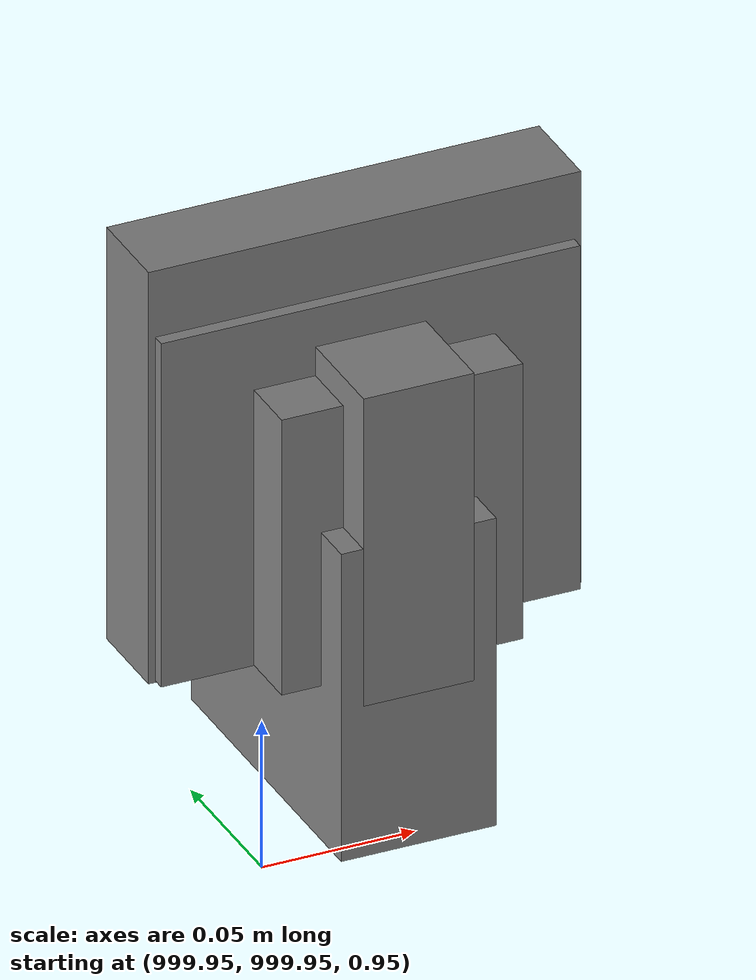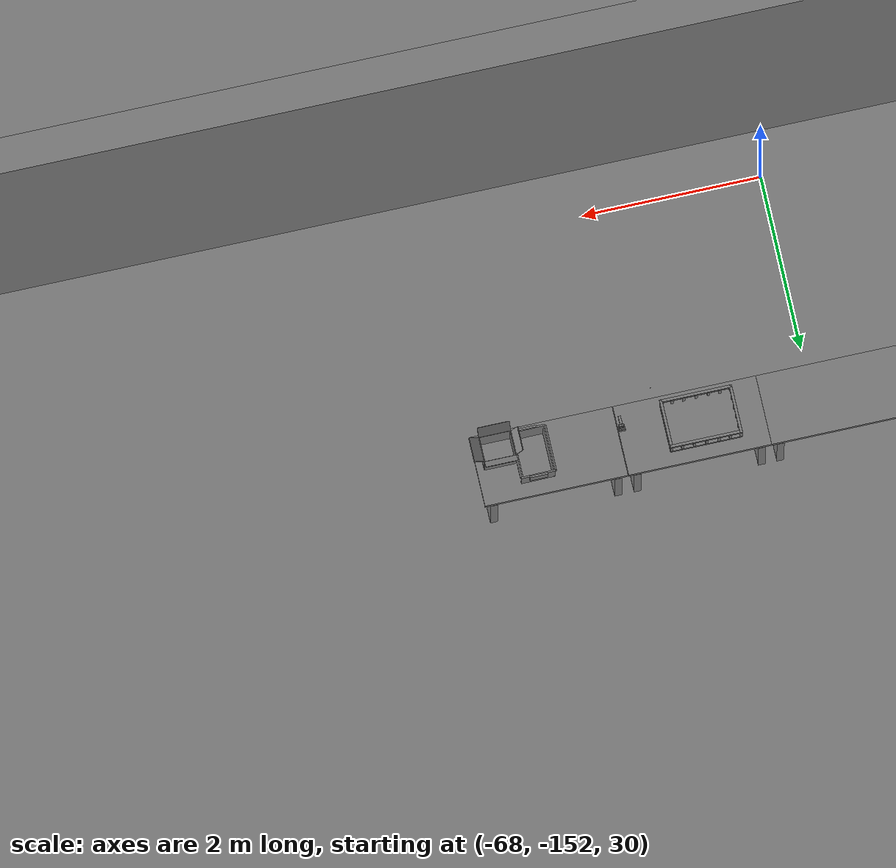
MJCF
<mujoco>
    <option gravity="0.000000000 0.000000000 -9.810000420" timestep="0.0049999999" integrator="implicitfast" density="1.225" viscosity="1.8000001e-05" noslip_iterations="10" iterations="100" sdf_iterations="50">
        <flag multiccd="disable"/>
    </option>
    <size memory="1000M"/>
    <compiler coordinate="local"/>
    <worldbody>
        <light cutoff="30" pos="0 1 1" dir="0 -1 -2"/>
        <light cutoff="30" pos="0 -1 1" dir="0 1 -2"/>
        <body pos="1000.000000000 999.999938965 1.000000000" euler="0.000000000 0.000000000 180.000000000" name="openloong_gripper_2f85_fix_base_usda_intelcore_i5">
            <geom contype="1" conaffinity="1" density="1000" type="box" material="" rgba="0.500000000 0.500000000 0.500000000 1.000000000" solimp="0.899999976 0.949999988 0.001000000" friction="1.000000000 0.005000000 0.000100000" solref="0.020000000 1.000000000" margin="0" condim="3" group="0" pos="0.000000000 0.000000000 0.051722717" quat="0.707106709 0.000000000 0.000000000 -0.707106769" size="0.052800000 0.018080002 0.052800000" name="openloong_gripper_2f85_fix_base_usda_geom_469C2108_E5E4_4800_BC83_A707F8F88285"/>
            <freejoint name="openloong_gripper_2f85_fix_base_usda_intelcore_i5_joint"/>
            <site size="0.005000000 0.005000000 0.005000000" rgba="0.500000000 0.500000000 0.500000000 1.000000000" pos="0.000000000 0.000000000 0.000000000" quat="0.999961913 0.008726534 0.000000000 0.000000000" group="0" type="sphere" name="openloong_gripper_2f85_fix_base_usda_intelcore_i5site"/>
        </body>
        <body pos="1000.000000000 1000.000000000 1.000000000" euler="0.000000000 0.000000000 180.000000000" name="openloong_gripper_2f85_fix_base_usda_battery_01">
            <geom contype="1" conaffinity="1" density="1000" type="box" material="" rgba="0.500000000 0.500000000 0.500000000 1.000000000" solimp="0.899999976 0.949999988 0.001000000" friction="1.000000000 0.005000000 0.000100000" solref="0.020000000 1.000000000" margin="0" condim="3" group="0" pos="-0.011123657 -0.041940309 0.101691343" quat="1.000000000 0.000000000 0.000000000 0.000000000" size="0.010800000 0.003375000 0.004725000" name="openloong_gripper_2f85_fix_base_usda_geom_D34DF235_502F_4E8C_B98E_F6494BFAAA78"/>
            <geom contype="1" conaffinity="1" density="1000" type="box" material="" rgba="0.500000000 0.500000000 0.500000000 1.000000000" solimp="0.899999976 0.949999988 0.001000000" friction="1.000000000 0.005000000 0.000100000" solref="0.020000000 1.000000000" margin="0" condim="3" group="0" pos="-0.010876465 -0.044247437 0.047066893" quat="0.998702705 -0.050920475 0.000000000 0.000000000" size="0.009450001 0.002700000 0.024975000" name="openloong_gripper_2f85_fix_base_usda_geom_50035879_DAF5_4F67_B96B_C7AAEDF87417"/>
            <geom contype="1" conaffinity="1" density="1000" type="box" material="" rgba="0.500000000 0.500000000 0.500000000 1.000000000" solimp="0.899999976 0.949999988 0.001000000" friction="1.000000000 0.005000000 0.000100000" solref="0.020000000 1.000000000" margin="0" condim="3" group="0" pos="-0.001235962 -0.000659180 0.047381196" quat="1.000000000 0.000000000 0.000000000 0.000000000" size="0.039420001 0.039150000 0.047250003" name="openloong_gripper_2f85_fix_base_usda_geom_9489107F_24C7_4109_8525_25C74A377D33"/>
            <geom contype="1" conaffinity="1" density="1000" type="box" material="" rgba="0.500000000 0.500000000 0.500000000 1.000000000" solimp="0.899999976 0.949999988 0.001000000" friction="1.000000000 0.005000000 0.000100000" solref="0.020000000 1.000000000" margin="0" condim="3" group="0" pos="-0.010876465 -0.039138794 0.009851727" quat="1.000000000 0.000000000 0.000000000 0.000000000" size="0.009450001 0.010800000 0.013500000" name="openloong_gripper_2f85_fix_base_usda_geom_DF4CA859_2815_4B34_A7BC_EE21B4077F11"/>
            <geom contype="1" conaffinity="1" density="1000" type="box" material="" rgba="0.500000000 0.500000000 0.500000000 1.000000000" solimp="0.899999976 0.949999988 0.001000000" friction="1.000000000 0.005000000 0.000100000" solref="0.020000000 1.000000000" margin="0" condim="3" group="0" pos="-0.010876465 -0.041528322 0.071508206" quat="1.000000000 0.000000000 0.000000000 0.000000000" size="0.009450001 0.002700000 0.027000001" name="openloong_gripper_2f85_fix_base_usda_geom_9EE0A7A6_21C9_43E9_AF72_300416A5D9F8"/>
            <freejoint name="openloong_gripper_2f85_fix_base_usda_battery_01_joint"/>
            <site size="0.005000000 0.005000000 0.005000000" rgba="0.500000000 0.500000000 0.500000000 1.000000000" pos="0.000000000 0.000000000 0.000000000" quat="0.999961913 0.008726500 0.000000000 0.000000000" group="0" type="sphere" name="openloong_gripper_2f85_fix_base_usda_battery_01site"/>
        </body>
        <body pos="-65.984535217 -149.097457886 31.164098740" euler="-88.015914917 23.450534821 57.347694397" mocap="true" name="spotlight3_SpotLight"/>
        <body pos="1000.000000000 1000.000000000 1.000000000" euler="0.000000000 0.000000000 180.000000000" name="openloong_gripper_2f85_fix_base_usda_cpu_fan">
            <geom contype="1" conaffinity="1" density="1000" type="box" material="" rgba="0.500000000 0.500000000 0.500000000 1.000000000" solimp="0.899999976 0.949999988 0.001000000" friction="1.000000000 0.005000000 0.000100000" solref="0.020000000 1.000000000" margin="0" condim="3" group="0" pos="0.000000000 0.000000000 0.070034981" quat="0.000000000 0.000000000 0.000000000 1.000000000" size="0.070700005 0.014699999 0.070700005" name="openloong_gripper_2f85_fix_base_usda_geom_35719F53_7E71_4E5D_8861_D8E33F08D8DA"/>
            <freejoint name="openloong_gripper_2f85_fix_base_usda_cpu_fan_joint"/>
            <site size="0.005000000 0.005000000 0.005000000" rgba="0.500000000 0.500000000 0.500000000 1.000000000" pos="0.000000000 0.000000000 0.000000000" quat="0.999961913 0.008726535 0.000000000 0.000000000" group="0" type="sphere" name="openloong_gripper_2f85_fix_base_usda_cpu_fancsite"/>
        </body>
        <body pos="1000.000000000 1000.000000000 1.000000000" euler="0.000000000 0.000000000 180.000000000" name="openloong_gripper_2f85_fix_base_usda_wifi_box">
            <geom contype="1" conaffinity="1" density="1000" type="box" material="" rgba="0.500000000 0.500000000 0.500000000 1.000000000" solimp="0.899999976 0.949999988 0.001000000" friction="1.000000000 0.005000000 0.000100000" solref="0.020000000 1.000000000" margin="0" condim="3" group="0" pos="0.000000000 0.000000000 0.058978677" quat="0.000000000 0.000000047 0.000000000 1.000000000" size="0.068499997 0.018999999 0.059000000" name="openloong_gripper_2f85_fix_base_usda_geom_6B00081A_524B_4168_ABDF_AC039C300270"/>
            <freejoint name="openloong_gripper_2f85_fix_base_usda_wifi_box_joint"/>
            <site size="0.005000000 0.005000000 0.005000000" rgba="0.500000000 0.500000000 0.500000000 1.000000000" pos="0.000000000 0.000000000 0.000000000" quat="0.999961913 0.008726500 0.000000000 0.000000000" group="0" type="sphere" name="openloong_gripper_2f85_fix_base_usda_wifi_boxsite"/>
        </body>
        <body pos="-66.160903931 -149.320098877 31.171010971" euler="57.955989838 46.676006317 16.180814743" mocap="true" name="spotlight6_SpotLight"/>
        <body pos="1000.000000000 1000.000000000 1.000000000" euler="0.000011953 0.000005123 -179.999984741" name="openloong_gripper_2f85_fix_base_usda_intel_box">
            <geom contype="1" conaffinity="1" density="1000" type="box" material="" rgba="0.500000000 0.500000000 0.500000000 1.000000000" solimp="0.899999976 0.949999988 0.001000000" friction="1.000000000 0.005000000 0.000100000" solref="0.020000000 1.000000000" margin="0" condim="3" group="0" pos="0.000000000 -0.000067139 0.000082284" quat="0.707106709 0.000000225 0.000000253 0.707106650" size="0.052800003 0.025300000 0.052800003" name="openloong_gripper_2f85_fix_base_usda_geom_3AD39BCB_22D5_4E28_BAF3_D6D37BA57BB8"/>
            <freejoint name="openloong_gripper_2f85_fix_base_usda_intel_box_joint"/>
            <site size="0.005000000 0.005000000 0.005000000" rgba="0.500000000 0.500000000 0.500000000 1.000000000" pos="0.000000000 0.000000000 0.000000000" quat="0.999961913 0.008726500 0.000000000 0.000000000" group="0" type="sphere" name="openloong_gripper_2f85_fix_base_usda_intel_boxsite"/>
        </body>
        <body pos="-66.350006104 -148.896255493 31.164852142" euler="-160.286193848 83.042778015 -61.758983612" mocap="true" name="spotlight1_SpotLight"/>
        <body pos="-64.866622925 -149.383972168 30.183746338" euler="89.999984741 89.999946594 0.000000000" name="openloong_gripper_2f85_fix_base_usda_bluebox_01">
            <geom contype="1" conaffinity="1" density="1000" type="box" material="" rgba="0.500000000 0.500000000 0.500000000 1.000000000" solimp="0.899999976 0.949999988 0.001000000" friction="1.000000000 0.005000000 0.000100000" solref="0.020000000 1.000000000" margin="0" condim="3" group="0" pos="0.276580811 0.187225342 0.000068665" quat="0.707106948 0.000077471 0.707106352 0.000077486" size="0.100000001 0.057999998 0.010000000" name="openloong_gripper_2f85_fix_base_usda_geom_BFD0091B_9010_471B_806C_2F97246173B8"/>
            <geom contype="1" conaffinity="1" density="1000" type="box" material="" rgba="0.500000000 0.500000000 0.500000000 1.000000000" solimp="0.899999976 0.949999988 0.001000000" friction="1.000000000 0.005000000 0.000100000" solref="0.020000000 1.000000000" margin="0" condim="3" group="0" pos="0.000000000 0.002883911 0.000000000" quat="0.999999881 0.000000000 0.000000000 0.000000000" size="0.254000008 0.003000000 0.172000006" name="openloong_gripper_2f85_fix_base_usda_geom_2639717F_B48D_47CD_89B1_B329FFCBF084"/>
            <geom contype="1" conaffinity="1" density="1000" type="box" material="" rgba="0.500000000 0.500000000 0.500000000 1.000000000" solimp="0.899999976 0.949999988 0.001000000" friction="1.000000000 0.005000000 0.000100000" solref="0.020000000 1.000000000" margin="0" condim="3" group="0" pos="0.000000000 0.124874115 0.173484802" quat="0.999796331 0.020176515 -0.000000015 0.000000030" size="0.259999990 0.119999997 0.007000000" name="openloong_gripper_2f85_fix_base_usda_geom_A4B5DDB5_07B0_46A1_B026_F3CA5C6D0B5E"/>
            <geom contype="1" conaffinity="1" density="1000" type="box" material="" rgba="0.500000000 0.500000000 0.500000000 1.000000000" solimp="0.899999976 0.949999988 0.001000000" friction="1.000000000 0.005000000 0.000100000" solref="0.020000000 1.000000000" margin="0" condim="3" group="0" pos="0.000000000 0.124874115 -0.173469543" quat="0.999796331 -0.020176545 -0.000000015 0.000000000" size="0.259999990 0.119999997 0.007000000" name="openloong_gripper_2f85_fix_base_usda_geom_885A9002_2F22_412E_B8BB_3509AA05FBD0"/>
            <geom contype="1" conaffinity="1" density="1000" type="box" material="" rgba="0.500000000 0.500000000 0.500000000 1.000000000" solimp="0.899999976 0.949999988 0.001000000" friction="1.000000000 0.005000000 0.000100000" solref="0.020000000 1.000000000" margin="0" condim="3" group="0" pos="0.000000000 0.214008331 0.188980103" quat="0.999912977 0.013176724 0.000000015 0.000000000" size="0.259999990 0.029999999 0.012500000" name="openloong_gripper_2f85_fix_base_usda_geom_12BAFCE2_A9C6_4EE8_8209_404CB2BDEA44"/>
            <geom contype="1" conaffinity="1" density="1000" type="box" material="" rgba="0.500000000 0.500000000 0.500000000 1.000000000" solimp="0.899999976 0.949999988 0.001000000" friction="1.000000000 0.005000000 0.000100000" solref="0.020000000 1.000000000" margin="0" condim="3" group="0" pos="-0.258361816 0.125289917 0.001876831" quat="0.702796936 -0.020792112 0.710783124 0.020769298" size="0.189999998 0.119999997 0.009000000" name="openloong_gripper_2f85_fix_base_usda_geom_895A5490_2D86_4EC7_82B9_155909A6192C"/>
            <geom contype="1" conaffinity="1" density="1000" type="box" material="" rgba="0.500000000 0.500000000 0.500000000 1.000000000" solimp="0.899999976 0.949999988 0.001000000" friction="1.000000000 0.005000000 0.000100000" solref="0.020000000 1.000000000" margin="0" condim="3" group="0" pos="0.000000000 0.214008331 -0.188980103" quat="0.999912977 -0.013176769 0.000000030 0.000000015" size="0.259999990 0.029999999 0.012500000" name="openloong_gripper_2f85_fix_base_usda_geom_61EFF9C5_9BCA_4750_9A94_E4F9131CFA65"/>
            <geom contype="1" conaffinity="1" density="1000" type="box" material="" rgba="0.500000000 0.500000000 0.500000000 1.000000000" solimp="0.899999976 0.949999988 0.001000000" friction="1.000000000 0.005000000 0.000100000" solref="0.020000000 1.000000000" margin="0" condim="3" group="0" pos="-0.276611328 0.187225342 0.000068665" quat="0.707106650 0.000077441 0.707106709 0.000077456" size="0.100000001 0.057999998 0.010000000" name="openloong_gripper_2f85_fix_base_usda_geom_60B7AE77_9810_4DAE_8E6F_6BBBFF5634FA"/>
            <geom contype="1" conaffinity="1" density="1000" type="box" material="" rgba="0.500000000 0.500000000 0.500000000 1.000000000" solimp="0.899999976 0.949999988 0.001000000" friction="1.000000000 0.005000000 0.000100000" solref="0.020000000 1.000000000" margin="0" condim="3" group="0" pos="0.258331299 0.125289917 0.001876831" quat="0.702851415 0.018856421 0.710823774 -0.019329369" size="0.189999998 0.119999997 0.009000000" name="openloong_gripper_2f85_fix_base_usda_geom_741844DB_C2F5_4B6E_AA21_A2723EF6F926"/>
            <freejoint name="openloong_gripper_2f85_fix_base_usda_bluebox_01_joint"/>
            <site size="0.005000000 0.005000000 0.005000000" rgba="0.500000000 0.500000000 0.500000000 1.000000000" pos="0.000000000 0.000000000 0.000000000" quat="0.999961913 0.008726534 0.000000000 0.000000000" group="0" type="sphere" name="openloong_gripper_2f85_fix_base_usda_bluebox_01site"/>
        </body>
        <body pos="-64.496299744 -149.491867065 30.235729218" euler="0.000000000 0.000000000 89.999946594" name="openloong_gripper_2f85_fix_base_usda_cardboardbox_01">
            <geom contype="1" conaffinity="1" density="1000" type="box" material="" rgba="0.500000000 0.500000000 0.500000000 1.000000000" solimp="0.899999976 0.949999988 0.001000000" friction="1.000000000 0.005000000 0.000100000" solref="0.020000000 1.000000000" margin="0" condim="3" group="0" pos="-0.003166199 -0.004086494 0.005052090" quat="1.000000000 0.000000000 0.000000000 0.000000000" size="0.142499998 0.177500010 0.005000000" name="openloong_gripper_2f85_fix_base_usda_geom_41C8ADEC_A75E_470F_B61F_66FDDDE33783"/>
            <geom contype="1" conaffinity="1" density="1000" type="box" material="" rgba="0.500000000 0.500000000 0.500000000 1.000000000" solimp="0.899999976 0.949999988 0.001000000" friction="1.000000000 0.005000000 0.000100000" solref="0.020000000 1.000000000" margin="0" condim="3" group="0" pos="-0.003166199 0.170316696 0.150570869" quat="1.000000000 0.000000000 0.000000000 0.000000000" size="0.142499998 0.005000000 0.149999991" name="openloong_gripper_2f85_fix_base_usda_geom_B3D2D184_2860_4D40_9C25_4CFA2362C476"/>
            <geom contype="1" conaffinity="1" density="1000" type="box" material="" rgba="0.500000000 0.500000000 0.500000000 1.000000000" solimp="0.899999976 0.949999988 0.001000000" friction="1.000000000 0.005000000 0.000100000" solref="0.020000000 1.000000000" margin="0" condim="3" group="0" pos="-0.147399902 -0.005307198 0.150570869" quat="1.000000000 0.000000000 0.000000000 0.000000000" size="0.005000000 0.177500010 0.149999991" name="openloong_gripper_2f85_fix_base_usda_geom_381598DF_456E_46A7_9A59_FD8274599378"/>
            <geom contype="1" conaffinity="1" density="1000" type="box" material="" rgba="0.500000000 0.500000000 0.500000000 1.000000000" solimp="0.899999976 0.949999988 0.001000000" friction="1.000000000 0.005000000 0.000100000" solref="0.020000000 1.000000000" margin="0" condim="3" group="0" pos="0.140275955 -0.005307198 0.150570869" quat="1.000000000 0.000000000 0.000000000 0.000000000" size="0.005000000 0.177500010 0.149999991" name="openloong_gripper_2f85_fix_base_usda_geom_D7E77F5F_8D1B_4696_BEF2_C1855F586992"/>
            <geom contype="1" conaffinity="1" density="1000" type="box" material="" rgba="0.500000000 0.500000000 0.500000000 1.000000000" solimp="0.899999976 0.949999988 0.001000000" friction="1.000000000 0.005000000 0.000100000" solref="0.020000000 1.000000000" margin="0" condim="3" group="0" pos="-0.003166199 -0.181550980 0.150570869" quat="1.000000000 0.000000000 0.000000000 0.000000000" size="0.142499998 0.005000000 0.149999991" name="openloong_gripper_2f85_fix_base_usda_geom_1E1B4E03_08A4_428B_9C70_090A41B69031"/>
            <freejoint name="openloong_gripper_2f85_fix_base_usda_cardboardbox_01_joint"/>
            <site size="0.005000000 0.005000000 0.005000000" rgba="0.500000000 0.500000000 0.500000000 1.000000000" pos="0.000000000 0.000000000 0.000000000" quat="0.999961913 0.008726535 0.000000000 0.000000000" group="0" type="sphere" name="openloong_gripper_2f85_fix_base_usda_site_79141208_746A_442B_A7EC_025374F895A8"/>
            <body pos="0.139160156 -0.004048347 0.301930904" euler="-179.999954224 49.383502960 179.999954224" name="openloong_gripper_2f85_fix_base_usda_A1_006">
                <geom contype="1" conaffinity="1" density="1000" type="box" material="" rgba="0.500000000 0.500000000 0.500000000 1.000000000" solimp="0.899999976 0.949999988 0.001000000" friction="1.000000000 0.005000000 0.000100000" solref="0.020000000 1.000000000" margin="0" condim="3" group="0" pos="-0.071587563 0.000009537 0.001745224" quat="0.999999881 0.000000000 0.000000000 0.000000000" size="0.071249999 0.179999992 0.002500000" name="openloong_gripper_2f85_fix_base_usda_geom_38C68C6E_17D8_4AFC_A343_8C570459133C"/>
                <joint armature="0" stiffness="0.07" damping="0.0099999998" axis="0.000000 1.000000 0.000000" type="hinge" name="openloong_gripper_2f85_fix_base_usda_A1_006"/>
            </body>
            <body pos="-0.145902634 -0.004086494 0.301938057" euler="-180.000000000 -60.000011444 -180.000000000" name="openloong_gripper_2f85_fix_base_usda_A2_006">
                <geom contype="1" conaffinity="1" density="1000" type="box" material="" rgba="0.500000000 0.500000000 0.500000000 1.000000000" solimp="0.899999976 0.949999988 0.001000000" friction="1.000000000 0.005000000 0.000100000" solref="0.020000000 1.000000000" margin="0" condim="3" group="0" pos="0.071268082 0.000009537 0.002717972" quat="0.000002921 0.000000000 -0.000000030 0.999999881" size="0.071249999 0.179999992 0.002500000" name="openloong_gripper_2f85_fix_base_usda_geom_F0F52944_4E2B_4BC1_9018_EA835C0B5A42"/>
                <joint armature="0" stiffness="0.07" damping="0.0099999998" axis="0.000000 1.000000 0.000000" type="hinge" name="openloong_gripper_2f85_fix_base_usda_A2_006"/>
            </body>
            <body pos="-0.003385544 0.175991058 0.301930904" euler="-125.858116150 -0.000004561 0.000002331" name="openloong_gripper_2f85_fix_base_usda_B2_006">
                <geom contype="1" conaffinity="1" density="1000" type="box" material="" rgba="0.500000000 0.500000000 0.500000000 1.000000000" solimp="0.899999976 0.949999988 0.001000000" friction="1.000000000 0.005000000 0.000100000" solref="0.020000000 1.000000000" margin="0" condim="3" group="0" pos="0.000009537 -0.070939064 -0.002470016" quat="0.999614120 0.027776197 -0.000000015 0.000000030" size="0.137500003 0.064999998 0.005000000" name="openloong_gripper_2f85_fix_base_usda_geom_02EE0474_27E7_45BB_A366_7BBB60DE8868"/>
                <joint armature="0" stiffness="0.07" damping="0.0099999998" axis="1.000000 0.000000 0.000000" type="hinge" name="openloong_gripper_2f85_fix_base_usda_B2_006"/>
            </body>
            <body pos="-0.003385544 -0.184140205 0.301938057" euler="147.805557251 0.000000000 0.000000000" name="openloong_gripper_2f85_fix_base_usda_B1_006">
                <geom contype="1" conaffinity="1" density="1000" type="box" material="" rgba="0.500000000 0.500000000 0.500000000 1.000000000" solimp="0.899999976 0.949999988 0.001000000" friction="1.000000000 0.005000000 0.000100000" solref="0.020000000 1.000000000" margin="0" condim="3" group="0" pos="-0.000028610 0.070202351 -0.002703667" quat="0.999614179 -0.027776167 0.000000000 0.000000000" size="0.137500003 0.064999998 0.005000000" name="openloong_gripper_2f85_fix_base_usda_geom_FA64A83D_7159_40AC_A730_BE96AE1CCE12"/>
                <joint armature="0" stiffness="0.07" damping="0.0099999998" axis="1.000000 0.000000 0.000000" type="hinge" name="openloong_gripper_2f85_fix_base_usda_B1_006"/>
            </body>
        </body>
        <body pos="-65.882858276 -149.481979370 30.229999542" euler="-64.487716675 0.000000000 0.000000000" name="openloong_gripper_2f85_fix_base_usda_Barcode">
            <geom contype="1" conaffinity="1" density="1000" type="box" material="" rgba="0.500000000 0.500000000 0.500000000 1.000000000" solimp="0.899999976 0.949999988 0.001000000" friction="1.000000000 0.005000000 0.000100000" solref="0.020000000 1.000000000" margin="0" condim="3" group="0" pos="0.000000000 0.013038635 0.001419067" quat="0.000000000 0.000000000 0.000000000 1.000000119" size="0.034000002 0.010000000 0.017999999" name="openloong_gripper_2f85_fix_base_usda_geom_55A472E2_6E1B_4596_A049_02A66357617C"/>
            <geom contype="1" conaffinity="1" density="1000" type="box" material="" rgba="0.500000000 0.500000000 0.500000000 1.000000000" solimp="0.899999976 0.949999988 0.001000000" friction="1.000000000 0.005000000 0.000100000" solref="0.020000000 1.000000000" margin="0" condim="3" group="0" pos="0.000000000 -0.035301208 -0.007095337" quat="0.000000000 0.000000000 -0.043619365 0.999048233" size="0.028999999 0.010000000 0.020000000" name="openloong_gripper_2f85_fix_base_usda_geom_8AD8D27D_FE31_43F5_B373_EEDF31125184"/>
            <geom contype="1" conaffinity="1" density="1000" type="box" material="" rgba="0.500000000 0.500000000 0.500000000 1.000000000" solimp="0.899999976 0.949999988 0.001000000" friction="1.000000000 0.005000000 0.000100000" solref="0.020000000 1.000000000" margin="0" condim="3" group="0" pos="0.000000000 -0.043411255 -0.011749268" quat="0.922262907 0.386563420 0.000000000 0.000000000" size="0.026000001 0.010000000 0.020000000" name="openloong_gripper_2f85_fix_base_usda_geom_E90F90A9_7B9B_43D1_9E1D_8B8240D55279"/>
            <geom contype="1" conaffinity="1" density="1000" type="box" material="" rgba="0.500000000 0.500000000 0.500000000 1.000000000" solimp="0.899999976 0.949999988 0.001000000" friction="1.000000000 0.005000000 0.000100000" solref="0.020000000 1.000000000" margin="0" condim="3" group="0" pos="0.000000000 -0.016967773 -0.031860352" quat="0.000000000 0.000000000 0.000000000 1.000000119" size="0.008000000 0.010000000 0.013000000" name="openloong_gripper_2f85_fix_base_usda_geom_03A44F87_C2E2_42CE_BC4F_C9408EC67BB1"/>
            <geom contype="1" conaffinity="1" density="1000" type="box" material="" rgba="0.500000000 0.500000000 0.500000000 1.000000000" solimp="0.899999976 0.949999988 0.001000000" friction="1.000000000 0.005000000 0.000100000" solref="0.020000000 1.000000000" margin="0" condim="3" group="0" pos="0.000000000 -0.001869202 0.000312805" quat="0.953716993 0.300705761 0.000000000 0.000000000" size="0.032000002 0.010000000 0.018999999" name="openloong_gripper_2f85_fix_base_usda_geom_52AD924A_A1A7_4836_8A73_1168C6FD9D76"/>
            <geom contype="1" conaffinity="1" density="1000" type="box" material="" rgba="0.500000000 0.500000000 0.500000000 1.000000000" solimp="0.899999976 0.949999988 0.001000000" friction="1.000000000 0.005000000 0.000100000" solref="0.020000000 1.000000000" margin="0" condim="3" group="0" pos="0.000000000 -0.019531250 -0.003173828" quat="0.953716993 0.300705761 0.000000000 0.000000000" size="0.030999999 0.010000000 0.020000000" name="openloong_gripper_2f85_fix_base_usda_geom_BF8B1EE3_ACE6_4E58_A953_6AC2BFFF4F44"/>
            <geom contype="1" conaffinity="1" density="1000" type="box" material="" rgba="0.500000000 0.500000000 0.500000000 1.000000000" solimp="0.899999976 0.949999988 0.001000000" friction="1.000000000 0.005000000 0.000100000" solref="0.020000000 1.000000000" margin="0" condim="3" group="0" pos="0.000000000 -0.035301208 -0.007095337" quat="0.953716993 0.300705761 0.000000000 0.000000000" size="0.028999999 0.010000000 0.020000000" name="openloong_gripper_2f85_fix_base_usda_geom_5CE3C612_172F_4CFD_96B4_B776315F0A8E"/>
            <geom contype="1" conaffinity="1" density="1000" type="box" material="" rgba="0.500000000 0.500000000 0.500000000 1.000000000" solimp="0.899999976 0.949999988 0.001000000" friction="1.000000000 0.005000000 0.000100000" solref="0.020000000 1.000000000" margin="0" condim="3" group="0" pos="0.000000000 -0.042617798 -0.071121216" quat="0.000000000 0.000000000 0.000000000 1.000000119" size="0.013000000 0.021000000 0.059999999" name="openloong_gripper_2f85_fix_base_usda_geom_F6A39F57_9B6A_4F02_810A_7F906DEC7816"/>
            <freejoint name="openloong_gripper_2f85_fix_base_usda_Barcode_joint"/>
            <site size="0.005000000 0.005000000 0.005000000" rgba="0.500000000 0.500000000 0.500000000 1.000000000" pos="0.000000000 0.000000000 0.000000000" quat="1.000000000 0.000000000 0.000000000 0.000000000" group="0" type="sphere" name="openloong_gripper_2f85_fix_base_usda_Barcode_site"/>
        </body>
        <body pos="-66.745018005 -149.392349243 30.184000015" euler="0.000000000 0.000000000 89.999946594" name="[22330762710663]_Basket_01">
            <geom contype="1" conaffinity="1" density="1000" type="box" material="" rgba="0.500000000 0.500000000 0.500000000 1.000000000" solimp="0.899999976 0.949999988 0.001000000" friction="1.000000000 0.005000000 0.000100000" solref="0.020000000 1.000000000" margin="0" condim="3" group="0" pos="-0.052425385 0.389207840 0.089787483" quat="0.707107008 0.000000000 0.000000000 0.707106411" size="0.014249999 0.014249999 0.059999999" name="[22330762710663]_geom_C558316A_7381_4D8F_B6CC_A97E6603CE8A"/>
            <geom contype="1" conaffinity="1" density="1000" type="box" material="" rgba="0.500000000 0.500000000 0.500000000 1.000000000" solimp="0.899999976 0.949999988 0.001000000" friction="1.000000000 0.005000000 0.000100000" solref="0.020000000 1.000000000" margin="0" condim="3" group="0" pos="0.264015198 -0.133043289 0.089787483" quat="0.707107008 0.000000000 0.000000000 0.707106411" size="0.014249999 0.014249999 0.059999999" name="[22330762710663]_geom_DC8535BC_E303_4887_92C9_B44697A700A1"/>
            <geom contype="1" conaffinity="1" density="1000" type="box" material="" rgba="0.500000000 0.500000000 0.500000000 1.000000000" solimp="0.899999976 0.949999988 0.001000000" friction="1.000000000 0.005000000 0.000100000" solref="0.020000000 1.000000000" margin="0" condim="3" group="0" pos="-0.264015198 -0.265548706 0.089793205" quat="0.707107008 0.000000000 0.000000000 0.707106411" size="0.014249999 0.014249999 0.059999999" name="[22330762710663]_geom_8A4A2E3B_8ABA_4931_A58C_1283CFA870EB"/>
            <geom contype="1" conaffinity="1" density="1000" type="box" material="" rgba="0.500000000 0.500000000 0.500000000 1.000000000" solimp="0.899999976 0.949999988 0.001000000" friction="1.000000000 0.005000000 0.000100000" solref="0.020000000 1.000000000" margin="0" condim="3" group="0" pos="-0.160263062 -0.389322281 0.089793205" quat="0.707107008 0.000000000 0.000000000 0.707106411" size="0.014249999 0.014249999 0.059999999" name="[22330762710663]_geom_847051DC_AF69_474C_BDC8_86DDF67BB23E"/>
            <geom contype="1" conaffinity="1" density="1000" type="box" material="" rgba="0.500000000 0.500000000 0.500000000 1.000000000" solimp="0.899999976 0.949999988 0.001000000" friction="1.000000000 0.005000000 0.000100000" solref="0.020000000 1.000000000" margin="0" condim="3" group="0" pos="0.162265778 -0.389322281 0.089787483" quat="0.707107008 0.000000000 0.000000000 0.707106411" size="0.014249999 0.014249999 0.059999999" name="[22330762710663]_geom_4E1E39FB_F04D_4663_AC58_78123C68AF77"/>
            <geom contype="1" conaffinity="1" density="1000" type="box" material="" rgba="0.500000000 0.500000000 0.500000000 1.000000000" solimp="0.899999976 0.949999988 0.001000000" friction="1.000000000 0.005000000 0.000100000" solref="0.020000000 1.000000000" margin="0" condim="3" group="0" pos="0.264015198 0.389207840 0.089787483" quat="0.707107008 0.000000000 0.000000000 0.707106411" size="0.014249999 0.014249999 0.059999999" name="[22330762710663]_geom_ACDB9DF3_C847_481B_85FA_353BF8A3DB44"/>
            <geom contype="1" conaffinity="1" density="1000" type="box" material="" rgba="0.500000000 0.500000000 0.500000000 1.000000000" solimp="0.899999976 0.949999988 0.001000000" friction="1.000000000 0.005000000 0.000100000" solref="0.020000000 1.000000000" margin="0" condim="3" group="0" pos="-0.264015198 -0.133043289 0.089793205" quat="0.707107008 0.000000000 0.000000000 0.707106411" size="0.014249999 0.014249999 0.059999999" name="[22330762710663]_geom_5DD152A8_4E77_45FA_B833_AF551605A331"/>
            <geom contype="1" conaffinity="1" density="1000" type="box" material="" rgba="0.500000000 0.500000000 0.500000000 1.000000000" solimp="0.899999976 0.949999988 0.001000000" friction="1.000000000 0.005000000 0.000100000" solref="0.020000000 1.000000000" margin="0" condim="3" group="0" pos="-0.264026642 0.269256592 0.089793205" quat="0.707107008 0.000000000 0.000000000 0.707106411" size="0.014249999 0.014249999 0.059999999" name="[22330762710663]_geom_5B6D8E15_7D5B_4C4D_A19B_A23777CF296F"/>
            <geom contype="1" conaffinity="1" density="1000" type="box" material="" rgba="0.500000000 0.500000000 0.500000000 1.000000000" solimp="0.899999976 0.949999988 0.001000000" friction="1.000000000 0.005000000 0.000100000" solref="0.020000000 1.000000000" margin="0" condim="3" group="0" pos="0.054462433 0.389207840 0.089787483" quat="0.707107008 0.000000000 0.000000000 0.707106411" size="0.014249999 0.014249999 0.059999999" name="[22330762710663]_geom_06DB31DF_B171_4991_BA65_36878404341C"/>
            <geom contype="1" conaffinity="1" density="1000" type="box" material="" rgba="0.500000000 0.500000000 0.500000000 1.000000000" solimp="0.899999976 0.949999988 0.001000000" friction="1.000000000 0.005000000 0.000100000" solref="0.020000000 1.000000000" margin="0" condim="3" group="0" pos="0.054462433 -0.389322281 0.089787483" quat="0.707107008 0.000000000 0.000000000 0.707106411" size="0.014249999 0.014249999 0.059999999" name="[22330762710663]_geom_5892A60B_F8C8_485F_B1B1_4F1D5330397D"/>
            <geom contype="1" conaffinity="1" density="1000" type="box" material="" rgba="0.500000000 0.500000000 0.500000000 1.000000000" solimp="0.899999976 0.949999988 0.001000000" friction="1.000000000 0.005000000 0.000100000" solref="0.020000000 1.000000000" margin="0" condim="3" group="0" pos="0.264015198 0.269256592 0.089793205" quat="0.707107008 0.000000000 0.000000000 0.707106411" size="0.014249999 0.014249999 0.059999999" name="[22330762710663]_geom_3E69734F_5852_4385_80A2_387748A63AC1"/>
            <geom contype="1" conaffinity="1" density="1000" type="box" material="" rgba="0.500000000 0.500000000 0.500000000 1.000000000" solimp="0.899999976 0.949999988 0.001000000" friction="1.000000000 0.005000000 0.000100000" solref="0.020000000 1.000000000" margin="0" condim="3" group="0" pos="0.264015198 -0.389322281 0.089787483" quat="0.707107008 0.000000000 0.000000000 0.707106411" size="0.014249999 0.014249999 0.059999999" name="[22330762710663]_geom_97BBA85E_D17A_44F1_A494_0D41AC1F6971"/>
            <geom contype="1" conaffinity="1" density="1000" type="box" material="" rgba="0.500000000 0.500000000 0.500000000 1.000000000" solimp="0.899999976 0.949999988 0.001000000" friction="1.000000000 0.005000000 0.000100000" solref="0.020000000 1.000000000" margin="0" condim="3" group="0" pos="0.000000000 0.000000000 0.015998840" quat="0.707107008 0.000000000 0.000000000 0.707106411" size="0.403499991 0.279000014 0.015750000" name="[22330762710663]_geom_68859426_E735_4363_B290_0F3A48B730CF"/>
            <geom contype="1" conaffinity="1" density="1000" type="box" material="" rgba="0.500000000 0.500000000 0.500000000 1.000000000" solimp="0.899999976 0.949999988 0.001000000" friction="1.000000000 0.005000000 0.000100000" solref="0.020000000 1.000000000" margin="0" condim="3" group="0" pos="0.000000000 -0.389476776 0.163619041" quat="0.707107008 0.000000000 0.000000000 0.707106411" size="0.015000000 0.277500004 0.015750000" name="[22330762710663]_geom_9A6F3EC9_4E40_47EF_840F_3C125E55A906"/>
            <geom contype="1" conaffinity="1" density="1000" type="box" material="" rgba="0.500000000 0.500000000 0.500000000 1.000000000" solimp="0.899999976 0.949999988 0.001000000" friction="1.000000000 0.005000000 0.000100000" solref="0.020000000 1.000000000" margin="0" condim="3" group="0" pos="0.162265778 0.389207840 0.089787483" quat="0.707107008 0.000000000 0.000000000 0.707106411" size="0.014249999 0.014249999 0.059999999" name="[22330762710663]_geom_658B35A6_1EB2_4C8C_817D_2EB219A39407"/>
            <geom contype="1" conaffinity="1" density="1000" type="box" material="" rgba="0.500000000 0.500000000 0.500000000 1.000000000" solimp="0.899999976 0.949999988 0.001000000" friction="1.000000000 0.005000000 0.000100000" solref="0.020000000 1.000000000" margin="0" condim="3" group="0" pos="0.000000000 0.389471054 0.163619041" quat="0.707107008 0.000000000 0.000000000 0.707106411" size="0.015000000 0.277500004 0.015750000" name="[22330762710663]_geom_659CC4D6_261C_4717_8ACF_2BE8076A439C"/>
            <geom contype="1" conaffinity="1" density="1000" type="box" material="" rgba="0.500000000 0.500000000 0.500000000 1.000000000" solimp="0.899999976 0.949999988 0.001000000" friction="1.000000000 0.005000000 0.000100000" solref="0.020000000 1.000000000" margin="0" condim="3" group="0" pos="-0.263511658 0.000000000 0.163619041" quat="0.707107008 0.000000000 0.000000000 0.707106411" size="0.403499991 0.015000000 0.015750000" name="[22330762710663]_geom_2BBC00BE_FB5D_44B2_B7D8_2A6FBA496492"/>
            <geom contype="1" conaffinity="1" density="1000" type="box" material="" rgba="0.500000000 0.500000000 0.500000000 1.000000000" solimp="0.899999976 0.949999988 0.001000000" friction="1.000000000 0.005000000 0.000100000" solref="0.020000000 1.000000000" margin="0" condim="3" group="0" pos="-0.264015198 0.141334534 0.089793205" quat="0.707107008 0.000000000 0.000000000 0.707106411" size="0.014249999 0.014249999 0.059999999" name="[22330762710663]_geom_4AE2B25D_DB61_47B5_8A37_FE77CFB6D7E5"/>
            <geom contype="1" conaffinity="1" density="1000" type="box" material="" rgba="0.500000000 0.500000000 0.500000000 1.000000000" solimp="0.899999976 0.949999988 0.001000000" friction="1.000000000 0.005000000 0.000100000" solref="0.020000000 1.000000000" margin="0" condim="3" group="0" pos="0.264015198 -0.265548706 0.089787483" quat="0.707107008 0.000000000 0.000000000 0.707106411" size="0.014249999 0.014249999 0.059999999" name="[22330762710663]_geom_0C299D68_823E_4E73_B712_77D98A107F43"/>
            <geom contype="1" conaffinity="1" density="1000" type="box" material="" rgba="0.500000000 0.500000000 0.500000000 1.000000000" solimp="0.899999976 0.949999988 0.001000000" friction="1.000000000 0.005000000 0.000100000" solref="0.020000000 1.000000000" margin="0" condim="3" group="0" pos="-0.160263062 0.389207840 0.089787483" quat="0.707107008 0.000000000 0.000000000 0.707106411" size="0.014249999 0.014249999 0.059999999" name="[22330762710663]_geom_0DA5DD8A_FDC7_4C82_9FF0_A35B0D342821"/>
            <geom contype="1" conaffinity="1" density="1000" type="box" material="" rgba="0.500000000 0.500000000 0.500000000 1.000000000" solimp="0.899999976 0.949999988 0.001000000" friction="1.000000000 0.005000000 0.000100000" solref="0.020000000 1.000000000" margin="0" condim="3" group="0" pos="-0.052425385 -0.389322281 0.089787483" quat="0.707107008 0.000000000 0.000000000 0.707106411" size="0.014249999 0.014249999 0.059999999" name="[22330762710663]_geom_7245E3AF_C8EF_4C2E_86CD_7BD4D38C315F"/>
            <geom contype="1" conaffinity="1" density="1000" type="box" material="" rgba="0.500000000 0.500000000 0.500000000 1.000000000" solimp="0.899999976 0.949999988 0.001000000" friction="1.000000000 0.005000000 0.000100000" solref="0.020000000 1.000000000" margin="0" condim="3" group="0" pos="-0.264026642 -0.389322281 0.089793205" quat="0.707107008 0.000000000 0.000000000 0.707106411" size="0.014249999 0.014249999 0.059999999" name="[22330762710663]_geom_E59E547E_90AB_416C_AD60_7C0191A891FA"/>
            <geom contype="1" conaffinity="1" density="1000" type="box" material="" rgba="0.500000000 0.500000000 0.500000000 1.000000000" solimp="0.899999976 0.949999988 0.001000000" friction="1.000000000 0.005000000 0.000100000" solref="0.020000000 1.000000000" margin="0" condim="3" group="0" pos="0.264015198 0.141334534 0.089787483" quat="0.707107008 0.000000000 0.000000000 0.707106411" size="0.014249999 0.014249999 0.059999999" name="[22330762710663]_geom_A70DF469_F6D0_4203_BCB3_20016E82C319"/>
            <geom contype="1" conaffinity="1" density="1000" type="box" material="" rgba="0.500000000 0.500000000 0.500000000 1.000000000" solimp="0.899999976 0.949999988 0.001000000" friction="1.000000000 0.005000000 0.000100000" solref="0.020000000 1.000000000" margin="0" condim="3" group="0" pos="-0.264015198 0.389207840 0.089793205" quat="0.707107008 0.000000000 0.000000000 0.707106411" size="0.014249999 0.014249999 0.059999999" name="[22330762710663]_geom_031C507F_594D_4CD4_B153_4919A4F18DE7"/>
            <geom contype="1" conaffinity="1" density="1000" type="box" material="" rgba="0.500000000 0.500000000 0.500000000 1.000000000" solimp="0.899999976 0.949999988 0.001000000" friction="1.000000000 0.005000000 0.000100000" solref="0.020000000 1.000000000" margin="0" condim="3" group="0" pos="0.264015198 0.004480362 0.089787483" quat="0.707107008 0.000000000 0.000000000 0.707106411" size="0.014249999 0.014249999 0.059999999" name="[22330762710663]_geom_E0AC9858_8E5E_4108_BEB7_75C9A38F4D50"/>
            <geom contype="1" conaffinity="1" density="1000" type="box" material="" rgba="0.500000000 0.500000000 0.500000000 1.000000000" solimp="0.899999976 0.949999988 0.001000000" friction="1.000000000 0.005000000 0.000100000" solref="0.020000000 1.000000000" margin="0" condim="3" group="0" pos="0.263694763 -0.000011444 0.163619041" quat="0.707107008 0.000000000 0.000000000 0.707106411" size="0.403499991 0.015000000 0.015750000" name="[22330762710663]_geom_0AF22BED_D1EB_4585_91B7_6824CFBDFF4A"/>
            <geom contype="1" conaffinity="1" density="1000" type="box" material="" rgba="0.500000000 0.500000000 0.500000000 1.000000000" solimp="0.899999976 0.949999988 0.001000000" friction="1.000000000 0.005000000 0.000100000" solref="0.020000000 1.000000000" margin="0" condim="3" group="0" pos="-0.264015198 0.004480362 0.089793205" quat="0.707107008 0.000000000 0.000000000 0.707106411" size="0.014249999 0.014249999 0.059999999" name="[22330762710663]_geom_1F89EE55_C73D_4343_A45A_33DA3D174B88"/>
            <freejoint name="[22330762710663]_joint_689407F8_CB13_4D07_B377_D32D66ADAA60"/>
        </body>
        <body pos="0.000000000 0.000000000 0.000000000" euler="0.000000000 0.000000000 0.000000000" name="Static Objects_Static Objects">
            <geom contype="1" conaffinity="1" density="1000" type="box" material="" rgba="0.500000000 0.500000000 0.500000000 1.000000000" solimp="0.899999976 0.949999988 0.001000000" friction="1.000000000 0.005000000 0.000100000" solref="0.020000000 1.000000000" margin="0" condim="3" group="0" pos="-67.544113159 -149.365814209 29.727830887" quat="0.500000417 0.499999970 0.499999553 0.499999970" size="0.381000012 0.319999993 0.041000001" name="Static Objects_geom_E2ACE92E_B643_4CE8_8927_C14D4764CC53"/>
            <geom contype="1" conaffinity="1" density="1000" type="box" material="" rgba="0.500000000 0.500000000 0.500000000 1.000000000" solimp="0.899999976 0.949999988 0.001000000" friction="1.000000000 0.005000000 0.000100000" solref="0.020000000 1.000000000" margin="0" condim="3" group="0" pos="-68.239501953 -149.365814209 30.086868286" quat="0.500000417 0.499999970 0.499999553 0.499999970" size="0.370999992 0.039500002 0.745000005" name="Static Objects_geom_60502CAF_915E_4B61_B71E_3C19B60757E1"/>
            <geom contype="1" conaffinity="1" density="1000" type="box" material="" rgba="0.500000000 0.500000000 0.500000000 1.000000000" solimp="0.899999976 0.949999988 0.001000000" friction="1.000000000 0.005000000 0.000100000" solref="0.020000000 1.000000000" margin="0" condim="3" group="0" pos="-68.239501953 -149.365814209 30.147235870" quat="0.500000417 0.499999970 0.499999553 0.499999970" size="0.400000006 0.022000000 0.800000012" name="Static Objects_geom_2AE768C6_2BDB_48E8_BB5E_543829E3E31D"/>
            <geom contype="1" conaffinity="1" density="1000" type="box" material="" rgba="0.500000000 0.500000000 0.500000000 1.000000000" solimp="0.899999976 0.949999988 0.001000000" friction="1.000000000 0.005000000 0.000100000" solref="0.020000000 1.000000000" margin="0" condim="3" group="0" pos="-68.934890747 -149.365814209 29.727830887" quat="0.500000417 0.499999970 0.499999553 0.499999970" size="0.381000012 0.319999993 0.041000001" name="Static Objects_geom_F42CFEB4_9B8B_485A_A40C_4CC4DDE25830"/>
            <geom contype="1" conaffinity="1" density="1000" type="box" material="" rgba="0.500000000 0.500000000 0.500000000 1.000000000" solimp="0.899999976 0.949999988 0.001000000" friction="1.000000000 0.005000000 0.000100000" solref="0.020000000 1.000000000" margin="0" condim="3" group="0" pos="-68.239501953 -149.365814209 29.561563492" quat="0.500000417 0.499999970 0.499999553 0.499999970" size="0.020000000 0.022000000 0.660000026" name="Static Objects_geom_0C509259_8672_4DDA_B81D_08F92C987725"/>
            <geom contype="1" conaffinity="1" density="1000" type="box" material="" rgba="0.500000000 0.500000000 0.500000000 1.000000000" solimp="0.899999976 0.949999988 0.001000000" friction="1.000000000 0.005000000 0.000100000" solref="0.020000000 1.000000000" margin="0" condim="3" group="0" pos="-65.945671082 -149.365814209 29.727830887" quat="0.500000417 0.499999970 0.499999553 0.499999970" size="0.381000012 0.319999993 0.041000001" name="Static Objects_geom_4A854DFD_D9C9_4E21_9CAD_4B2A781CE3E1"/>
            <geom contype="1" conaffinity="1" density="1000" type="box" material="" rgba="0.500000000 0.500000000 0.500000000 1.000000000" solimp="0.899999976 0.949999988 0.001000000" friction="1.000000000 0.005000000 0.000100000" solref="0.020000000 1.000000000" margin="0" condim="3" group="0" pos="-66.641059875 -149.365814209 30.086868286" quat="0.500000417 0.499999970 0.499999553 0.499999970" size="0.370999992 0.039500002 0.745000005" name="Static Objects_geom_BEAC2062_E9F8_4F8A_BEE6_BC7D95E8FBC9"/>
            <geom contype="1" conaffinity="1" density="1000" type="box" material="" rgba="0.500000000 0.500000000 0.500000000 1.000000000" solimp="0.899999976 0.949999988 0.001000000" friction="1.000000000 0.005000000 0.000100000" solref="0.020000000 1.000000000" margin="0" condim="3" group="0" pos="-66.641059875 -149.365814209 30.147235870" quat="0.500000417 0.499999970 0.499999553 0.499999970" size="0.400000006 0.022000000 0.800000012" name="Static Objects_geom_9534B283_D14B_47DC_A388_56784576479B"/>
            <geom contype="1" conaffinity="1" density="1000" type="box" material="" rgba="0.500000000 0.500000000 0.500000000 1.000000000" solimp="0.899999976 0.949999988 0.001000000" friction="1.000000000 0.005000000 0.000100000" solref="0.020000000 1.000000000" margin="0" condim="3" group="0" pos="-67.336448669 -149.365814209 29.727830887" quat="0.500000417 0.499999970 0.499999553 0.499999970" size="0.381000012 0.319999993 0.041000001" name="Static Objects_geom_472A1FD1_7E02_4D3A_A13E_524B1F257F59"/>
            <geom contype="1" conaffinity="1" density="1000" type="box" material="" rgba="0.500000000 0.500000000 0.500000000 1.000000000" solimp="0.899999976 0.949999988 0.001000000" friction="1.000000000 0.005000000 0.000100000" solref="0.020000000 1.000000000" margin="0" condim="3" group="0" pos="-66.641059875 -149.365814209 29.561563492" quat="0.500000417 0.499999970 0.499999553 0.499999970" size="0.020000000 0.022000000 0.660000026" name="Static Objects_geom_4565A749_6580_4968_99B2_9B5906A370CB"/>
            <geom contype="1" conaffinity="1" density="1000" type="box" material="" rgba="0.500000000 0.500000000 0.500000000 1.000000000" solimp="0.899999976 0.949999988 0.001000000" friction="1.000000000 0.005000000 0.000100000" solref="0.020000000 1.000000000" margin="0" condim="3" group="0" pos="-64.338577271 -149.365814209 29.727830887" quat="0.500000417 0.499999970 0.499999553 0.499999970" size="0.381000012 0.319999993 0.041000001" name="Static Objects_geom_1790B171_ED41_4214_A329_616E16366666"/>
            <geom contype="1" conaffinity="1" density="1000" type="box" material="" rgba="0.500000000 0.500000000 0.500000000 1.000000000" solimp="0.899999976 0.949999988 0.001000000" friction="1.000000000 0.005000000 0.000100000" solref="0.020000000 1.000000000" margin="0" condim="3" group="0" pos="-65.033966064 -149.365814209 30.086868286" quat="0.500000417 0.499999970 0.499999553 0.499999970" size="0.370999992 0.039500002 0.745000005" name="Static Objects_geom_53E8EE8F_4B11_43B3_BDB0_CBB2D17EB5AB"/>
            <geom contype="1" conaffinity="1" density="1000" type="box" material="" rgba="0.500000000 0.500000000 0.500000000 1.000000000" solimp="0.899999976 0.949999988 0.001000000" friction="1.000000000 0.005000000 0.000100000" solref="0.020000000 1.000000000" margin="0" condim="3" group="0" pos="-65.033966064 -149.365814209 30.147235870" quat="0.500000417 0.499999970 0.499999553 0.499999970" size="0.400000006 0.022000000 0.800000012" name="Static Objects_geom_059D3B89_E872_4808_B3E0_37C40B902867"/>
            <geom contype="1" conaffinity="1" density="1000" type="box" material="" rgba="0.500000000 0.500000000 0.500000000 1.000000000" solimp="0.899999976 0.949999988 0.001000000" friction="1.000000000 0.005000000 0.000100000" solref="0.020000000 1.000000000" margin="0" condim="3" group="0" pos="-65.729354858 -149.365814209 29.727830887" quat="0.500000417 0.499999970 0.499999553 0.499999970" size="0.381000012 0.319999993 0.041000001" name="Static Objects_geom_0AC73DF2_245C_4B69_B34A_C35A6A81AECC"/>
            <geom contype="1" conaffinity="1" density="1000" type="box" material="" rgba="0.500000000 0.500000000 0.500000000 1.000000000" solimp="0.899999976 0.949999988 0.001000000" friction="1.000000000 0.005000000 0.000100000" solref="0.020000000 1.000000000" margin="0" condim="3" group="0" pos="-65.033966064 -149.365814209 29.561563492" quat="0.500000417 0.499999970 0.499999553 0.499999970" size="0.020000000 0.022000000 0.660000026" name="Static Objects_geom_C5212713_729C_45BE_A0F0_94DA75BC5F0F"/>
            <geom contype="1" conaffinity="1" density="1000" type="box" material="" rgba="0.500000000 0.500000000 0.500000000 1.000000000" solimp="0.899999976 0.949999988 0.001000000" friction="1.000000000 0.005000000 0.000100000" solref="0.020000000 1.000000000" margin="0" condim="3" group="0" pos="-61.754566193 -137.853729248 33.906845093" quat="0.707107067 0.000000000 0.000000000 0.707106471" size="0.759999990 0.759999990 4.500000000" name="Static Objects_geom_D1DE38B6_6265_4AC7_AF55_88221853BDD2"/>
            <geom contype="1" conaffinity="1" density="1000" type="box" material="" rgba="0.500000000 0.500000000 0.500000000 1.000000000" solimp="0.899999976 0.949999988 0.001000000" friction="1.000000000 0.005000000 0.000100000" solref="0.020000000 1.000000000" margin="0" condim="3" group="0" pos="-57.511135101 -144.927108765 31.707921982" quat="1.000000000 0.000000000 0.000000000 0.000000000" size="0.200000003 8.000000000 2.299999952" name="Static Objects_geom_5A6A7694_3BF9_4FD9_91C7_EAA79BE1480F"/>
            <geom contype="1" conaffinity="1" density="1000" type="box" material="" rgba="0.500000000 0.500000000 0.500000000 1.000000000" solimp="0.899999976 0.949999988 0.001000000" friction="1.000000000 0.005000000 0.000100000" solref="0.020000000 1.000000000" margin="0" condim="3" group="0" pos="-80.517646790 -157.574050903 31.688196182" quat="0.707107067 0.000000000 0.000000000 0.707106471" size="0.600000024 0.600000024 2.299999952" name="Static Objects_geom_EAE7315C_825A_4BBA_9EEE_EF313929E66C"/>
            <geom contype="1" conaffinity="1" density="1000" type="box" material="" rgba="0.500000000 0.500000000 0.500000000 1.000000000" solimp="0.899999976 0.949999988 0.001000000" friction="1.000000000 0.005000000 0.000100000" solref="0.020000000 1.000000000" margin="0" condim="3" group="0" pos="-80.711044312 -147.414932251 31.666158676" quat="1.000000000 0.000000000 0.000000000 0.000000000" size="0.200000003 10.000000000 2.299999952" name="Static Objects_geom_BAB49345_0429_4574_AF3E_5EDEE378CB29"/>
            <geom contype="1" conaffinity="1" density="1000" type="box" material="" rgba="0.500000000 0.500000000 0.500000000 1.000000000" solimp="0.899999976 0.949999988 0.001000000" friction="1.000000000 0.005000000 0.000100000" solref="0.020000000 1.000000000" margin="0" condim="3" group="0" pos="-57.687217712 -137.434692383 31.688196182" quat="0.707107067 0.000000000 0.000000000 0.707106471" size="0.600000024 0.600000024 2.299999952" name="Static Objects_geom_7AB6E34D_629F_4771_AFBF_D194B063B1E4"/>
            <geom contype="1" conaffinity="1" density="1000" type="box" material="" rgba="0.500000000 0.500000000 0.500000000 1.000000000" solimp="0.899999976 0.949999988 0.001000000" friction="1.000000000 0.005000000 0.000100000" solref="0.020000000 1.000000000" margin="0" condim="3" group="0" pos="-69.537033081 -140.263229370 31.714921951" quat="0.707107067 0.000000000 0.000000000 0.707106471" size="0.759999990 4.500000000 2.299999952" name="Static Objects_geom_BEFC0180_5D6D_448D_A235_2BE6BDF2263F"/>
            <geom contype="1" conaffinity="1" density="1000" type="box" material="" rgba="0.500000000 0.500000000 0.500000000 1.000000000" solimp="0.899999976 0.949999988 0.001000000" friction="1.000000000 0.005000000 0.000100000" solref="0.020000000 1.000000000" margin="0" condim="3" group="0" pos="-80.073638916 -137.853713989 33.906845093" quat="0.707107067 0.000000000 0.000000000 0.707106471" size="0.759999990 0.759999990 4.500000000" name="Static Objects_geom_069DEB93_1570_4F31_8DA2_359AE7C72998"/>
            <geom contype="1" conaffinity="1" density="1000" type="box" material="" rgba="0.500000000 0.500000000 0.500000000 1.000000000" solimp="0.899999976 0.949999988 0.001000000" friction="1.000000000 0.005000000 0.000100000" solref="0.020000000 1.000000000" margin="0" condim="3" group="0" pos="-73.406707764 -155.734664917 31.707921982" quat="1.000000000 0.000000000 0.000000000 0.000000000" size="0.200000003 3.000000000 2.299999952" name="Static Objects_geom_A833A09C_2B6F_4BB2_A4B7_8347BBB74671"/>
            <geom contype="1" conaffinity="1" density="1000" type="box" material="" rgba="0.500000000 0.500000000 0.500000000 1.000000000" solimp="0.899999976 0.949999988 0.001000000" friction="1.000000000 0.005000000 0.000100000" solref="0.020000000 1.000000000" margin="0" condim="3" group="0" pos="-68.497543335 -137.448257446 31.707921982" quat="0.707107067 0.000000000 0.000000000 0.707106471" size="0.200000003 14.000000000 2.299999952" name="Static Objects_geom_9167BD03_FE13_450D_902C_9901B3DB14F2"/>
            <geom contype="1" conaffinity="1" density="1000" type="cylinder" material="" rgba="0.500000000 0.500000000 0.500000000 1.000000000" solimp="0.899999976 0.949999988 0.001000000" friction="1.000000000 0.005000000 0.000100000" solref="0.020000000 1.000000000" margin="0" condim="3" group="0" pos="-68.868522644 -142.134506226 31.711090088" quat="0.707107067 0.000000000 0.000000000 0.707106471" size="0.509999990 2.299999952 1.000000000" name="Static Objects_geom_24D176FE_0F36_4C46_AE9F_D5AF3183A39C"/>
            <geom contype="1" conaffinity="1" density="1000" type="plane" material="" rgba="0.500000000 0.500000000 0.500000000 1.000000000" solimp="0.899999976 0.949999988 0.001000000" friction="1.000000000 0.005000000 0.000100000" solref="0.020000000 1.000000000" margin="0" condim="3" group="0" pos="-72.873703003 -147.131927490 29.409669876" quat="1.000000000 0.000000000 0.000000000 0.000000000" size="18.000000000 14.000000000 1.000000000" name="Static Objects_geom_3CD28BBB_E406_467D_AF7B_471E9385315B"/>
            <geom contype="1" conaffinity="1" density="1000" type="box" material="" rgba="0.500000000 0.500000000 0.500000000 1.000000000" solimp="0.899999976 0.949999988 0.001000000" friction="1.000000000 0.005000000 0.000100000" solref="0.020000000 1.000000000" margin="0" condim="3" group="0" pos="-79.943580627 -157.782272339 31.707921982" quat="0.707107067 0.000000000 0.000000000 0.707106471" size="0.200000003 7.000000000 2.299999952" name="Static Objects_geom_8731F4D7_2285_431B_AF88_35712473CE0A"/>
            <geom contype="1" conaffinity="1" density="1000" type="box" material="" rgba="0.500000000 0.500000000 0.500000000 1.000000000" solimp="0.899999976 0.949999988 0.001000000" friction="1.000000000 0.005000000 0.000100000" solref="0.020000000 1.000000000" margin="0" condim="3" group="0" pos="-65.421028137 -152.903442383 31.707921982" quat="0.707107067 0.000000000 0.000000000 0.707106471" size="0.200000003 7.800000191 2.299999952" name="Static Objects_geom_FA2D5597_F514_4C54_A659_73693BB27D3F"/>
            <geom contype="1" conaffinity="1" density="1000" type="box" material="" rgba="0.500000000 0.500000000 0.500000000 1.000000000" solimp="0.899999976 0.949999988 0.001000000" friction="1.000000000 0.005000000 0.000100000" solref="0.020000000 1.000000000" margin="0" condim="3" group="0" pos="-74.776908875 -149.964416504 31.688196182" quat="1.000000000 0.000000000 0.000000000 0.000000000" size="0.600000024 0.409999996 2.299999952" name="Static Objects_geom_85C35022_4927_4638_934A_D962195C02AE"/>
            <geom contype="1" conaffinity="1" density="1000" type="cylinder" material="" rgba="0.500000000 0.500000000 0.500000000 1.000000000" solimp="0.899999976 0.949999988 0.001000000" friction="1.000000000 0.005000000 0.000100000" solref="0.020000000 1.000000000" margin="0" condim="3" group="0" pos="-60.161884308 -142.134506226 31.711090088" quat="0.707107067 0.000000000 0.000000000 0.707106471" size="0.509999990 2.299999952 1.000000000" name="Static Objects_geom_BDCC48F9_38AD_4DF2_94C3_B6A82AE5B73D"/>
            <geom contype="1" conaffinity="1" density="1000" type="cylinder" material="" rgba="0.500000000 0.500000000 0.500000000 1.000000000" solimp="0.899999976 0.949999988 0.001000000" friction="1.000000000 0.005000000 0.000100000" solref="0.020000000 1.000000000" margin="0" condim="3" group="0" pos="-75.382453918 -149.963455200 31.711090088" quat="0.707107067 0.000000000 0.000000000 0.707106471" size="0.409999996 2.299999952 1.000000000" name="Static Objects_geom_09295AE6_6F96_4CB8_903E_23E967531CE5"/>
            <geom contype="1" conaffinity="1" density="1000" type="cylinder" material="" rgba="0.500000000 0.500000000 0.500000000 1.000000000" solimp="0.899999976 0.949999988 0.001000000" friction="1.000000000 0.005000000 0.000100000" solref="0.020000000 1.000000000" margin="0" condim="3" group="0" pos="-74.154960632 -149.963455200 31.711090088" quat="0.707107067 0.000000000 0.000000000 0.707106471" size="0.409999996 2.299999952 1.000000000" name="Static Objects_geom_F960B729_F37F_4854_8C57_D4B60036A81D"/>
            <geom contype="1" conaffinity="1" density="1000" type="cylinder" material="" rgba="0.500000000 0.500000000 0.500000000 1.000000000" solimp="0.899999976 0.949999988 0.001000000" friction="1.000000000 0.005000000 0.000100000" solref="0.020000000 1.000000000" margin="0" condim="3" group="0" pos="-77.566612244 -142.134506226 31.711090088" quat="0.707107067 0.000000000 0.000000000 0.707106471" size="0.509999990 2.299999952 1.000000000" name="Static Objects_geom_62D54DCA_82A2_4A38_9B68_F65448A4F142"/>
        </body>
        <body pos="-66.291030884 -149.869689941 29.018842697" euler="0.000000000 0.000000000 89.999946594" mocap="true" name="openloong_gripper_2f85_fix_base_usda_leftHandMocap"/>
        <body pos="-66.291030884 -149.869689941 29.018842697" euler="0.000000000 0.000000000 89.999946594" mocap="true" name="openloong_gripper_2f85_fix_base_usda_rightHandMocap"/>
        <body pos="-66.291030884 -149.869689941 30.218843460" euler="0.000000000 0.000000000 89.999946594" name="openloong_gripper_2f85_fix_base_usda_base_link">
            <geom contype="1" conaffinity="1" density="1000" type="mesh" material="" rgba="0.783999979 0.783999979 0.783999979 1.000000000" solimp="0.899999976 0.949999988 0.001000000" friction="1.000000000 0.005000000 0.000100000" solref="0.020000000 1.000000000" margin="0" condim="3" group="3" mesh="base_link" pos="0.000000000 0.000000000 0.000000000" quat="1.000000000 0.000000000 0.000000000 0.000000000" size="1.000000000 1.000000000 1.000000000" name="openloong_gripper_2f85_fix_base_usda__geom_7_BAA7744C_0F30_4859_9B73_273F6799D223"/>
            <site size="0.005000000 0.005000000 0.005000000" rgba="0.500000000 0.500000000 0.500000000 1.000000000" pos="0.000000000 0.000000000 0.000000000" quat="1.000000000 0.000000000 0.000000000 0.000000000" group="0" type="sphere" name="openloong_gripper_2f85_fix_base_usda_imu"/>
            <inertial mass="22.447001" pos="-0.005664100 -0.001336700 0.238289997" diaginertia="0.374352545 0.277180195 0.220617250" quat="0.999247074 0.035235517 -0.015086859 0.006023135"/>
            <body pos="0.000000000 0.000000000 0.299997330" euler="0.000000000 0.000000000 0.000000000" name="openloong_gripper_2f85_fix_base_usda_dummy_body">
                <geom contype="1" conaffinity="1" density="1000" type="sphere" material="" rgba="0.783999979 0.783999979 0.783999979 1.000000000" solimp="0.899999976 0.949999988 0.001000000" friction="1.000000000 0.005000000 0.000100000" solref="0.020000000 1.000000000" margin="0" condim="3" group="3" pos="0.000000000 0.000000000 0.000000000" quat="1.000000000 0.000000000 0.000000000 0.000000000" size="0.010000000 0.000000000 0.000000000" name="openloong_gripper_2f85_fix_base_usda__geom_8_4B4DDD60_468D_4630_814E_F9641F8284EE"/>
                <joint armature="0.0099999998" stiffness="0" damping="0.1" axis="0.000000 0.000000 1.000000" type="hinge" name="openloong_gripper_2f85_fix_base_usda_dummy_joint"/>
                <site size="0.010000000 0.005000000 0.005000000" rgba="0.500000000 0.500000000 0.500000000 1.000000000" pos="0.000000000 0.000000000 0.000000000" quat="1.000000000 0.000000000 0.000000000 0.000000000" group="3" type="sphere" name="openloong_gripper_2f85_fix_base_usda_dummy_site"/>
            </body>
            <body pos="0.009002686 0.000000000 0.406400681" euler="0.000000000 0.000000000 0.000000000" name="openloong_gripper_2f85_fix_base_usda_Link_head_yaw">
                <geom contype="1" conaffinity="1" density="1000" type="mesh" material="" rgba="0.783999979 0.783999979 0.783999979 1.000000000" solimp="0.899999976 0.949999988 0.001000000" friction="1.000000000 0.005000000 0.000100000" solref="0.020000000 1.000000000" margin="0" condim="3" group="3" mesh="Link_head_yaw" pos="0.000000000 0.000000000 0.000000000" quat="1.000000000 0.000000000 0.000000000 0.000000000" size="1.000000000 1.000000000 1.000000000" name="openloong_gripper_2f85_fix_base_usda__geom_10_90A854AC_144F_402E_AC12_A46D35304B9B"/>
                <inertial mass="0.84249002" pos="0.000000000 -0.002081400 0.044801001" diaginertia="0.000700588 0.000629000 0.000553812" quat="0.706933022 -0.015675601 0.015677100 0.706933022"/>
                <body pos="0.000000000 -0.034599304 0.048500061" euler="0.000000000 0.000000000 0.000000000" name="openloong_gripper_2f85_fix_base_usda_Link_head_pitch">
                    <geom contype="1" conaffinity="1" density="1000" type="mesh" material="" rgba="0.783999979 0.783999979 0.783999979 1.000000000" solimp="0.899999976 0.949999988 0.001000000" friction="1.000000000 0.005000000 0.000100000" solref="0.020000000 1.000000000" margin="0" condim="3" group="3" mesh="Link_head_pitch" pos="0.000000000 0.000000000 0.000000000" quat="1.000000000 0.000000000 0.000000000 0.000000000" size="1.000000000 1.000000000 1.000000000" name="openloong_gripper_2f85_fix_base_usda__geom_12_EE4026CF_A1B4_4A7D_8B31_9052A7B24915"/>
                    <inertial mass="1.3943" pos="0.020569000 0.033004001 0.125000000" diaginertia="0.006381400 0.006289940 0.004481460" quat="0.973390222 0.008406822 0.228157058 0.019624906"/>
                    <body pos="0.000000000 0.029998779 0.000000000" euler="0.000000000 0.000000000 0.000000000" name="openloong_gripper_2f85_fix_base_usda_neck_center_body">
                        <site size="0.010000000 0.005000000 0.005000000" rgba="0.500000000 0.500000000 0.500000000 1.000000000" pos="0.000000000 0.000000000 0.000000000" quat="1.000000000 0.000000000 0.000000000 0.000000000" group="3" type="sphere" name="openloong_gripper_2f85_fix_base_usda_neck_center_site"/>
                        <body pos="0.020004272 0.000000000 0.149999619" euler="-0.000002229 39.998176575 -90.000205994" name="openloong_gripper_2f85_fix_base_usda_camera_head">
                            <site size="0.010000000 0.005000000 0.005000000" rgba="0.500000000 0.500000000 0.500000000 1.000000000" pos="0.000000000 0.000000000 0.000000000" quat="1.000000000 0.000000000 0.000000000 0.000000000" group="3" type="sphere" name="openloong_gripper_2f85_fix_base_usda_camera_head_site"/>
                        </body>
                    </body>
                </body>
            </body>
            <body pos="0.003997803 -0.161598206 0.392200470" euler="0.000000000 0.000000000 0.000000000" name="openloong_gripper_2f85_fix_base_usda_Link_arm_r_01">
                <geom contype="1" conaffinity="1" density="1000" type="mesh" material="" rgba="0.783999979 0.783999979 0.783999979 1.000000000" solimp="0.899999976 0.949999988 0.001000000" friction="1.000000000 0.005000000 0.000100000" solref="0.020000000 1.000000000" margin="0" condim="3" group="3" mesh="Link_arm_r_01" pos="0.000000000 0.000000000 0.000000000" quat="1.000000000 0.000000000 0.000000000 0.000000000" size="1.000000000 1.000000000 1.000000000" name="openloong_gripper_2f85_fix_base_usda__geom_14_89AB30DE_D24E_4E62_9E0D_CFE46EE234E9"/>
                <joint armature="0.0099999998" stiffness="0" damping="1" axis="0.000000 -1.000000 0.000000" limited="true" range="-170.000015259 170.000015259" type="hinge" name="openloong_gripper_2f85_fix_base_usda_J_arm_r_01"/>
                <inertial mass="0.75641" pos="0.004494600 -0.038293999 -0.000001874" diaginertia="0.000842990 0.000803050 0.000587120" quat="-0.000163502 0.707098067 0.000812463 0.707115054"/>
                <body pos="-0.041992188 -0.041000366 0.000000000" euler="0.000000000 0.000000000 0.000000000" name="openloong_gripper_2f85_fix_base_usda_Link_arm_r_02">
                    <geom contype="1" conaffinity="1" density="1000" type="mesh" material="" rgba="0.783999979 0.783999979 0.783999979 1.000000000" solimp="0.899999976 0.949999988 0.001000000" friction="1.000000000 0.005000000 0.000100000" solref="0.020000000 1.000000000" margin="0" condim="3" group="3" mesh="Link_arm_r_02" pos="0.000000000 0.000000000 0.000000000" quat="1.000000000 0.000000000 0.000000000 0.000000000" size="1.000000000 1.000000000 1.000000000" name="openloong_gripper_2f85_fix_base_usda__geom_16_1623825C_FF05_4A3F_97C5_4CB7205D092C"/>
                    <joint armature="0.0099999998" stiffness="0" damping="1" axis="-1.000000 0.000000 0.000000" limited="true" range="-105.000244141 105.000244141" type="hinge" name="openloong_gripper_2f85_fix_base_usda_J_arm_r_02"/>
                    <inertial mass="0.98500001" pos="0.041999999 -0.067430697 0.000000000" diaginertia="0.002262690 0.001730990 0.001154020" quat="0.500000000 0.500000000 -0.500000000 0.500000000"/>
                    <body pos="0.041992188 -0.122596741 0.000000000" euler="0.000000000 0.000000000 0.000000000" name="openloong_gripper_2f85_fix_base_usda_Link_arm_r_03">
                        <geom contype="1" conaffinity="1" density="1000" type="mesh" material="" rgba="0.783999979 0.783999979 0.783999979 1.000000000" solimp="0.899999976 0.949999988 0.001000000" friction="1.000000000 0.005000000 0.000100000" solref="0.020000000 1.000000000" margin="0" condim="3" group="3" mesh="Link_arm_r_03" pos="0.000000000 0.000000000 0.000000000" quat="1.000000000 0.000000000 0.000000000 0.000000000" size="1.000000000 1.000000000 1.000000000" name="openloong_gripper_2f85_fix_base_usda__geom_18_45DD7B89_A1AD_4396_9DA6_AE2180AE6CFF"/>
                        <joint armature="0.0099999998" stiffness="0" damping="1" axis="0.000000 -1.000000 0.000000" limited="true" range="-170.000015259 170.000015259" type="hinge" name="openloong_gripper_2f85_fix_base_usda_J_arm_r_03"/>
                        <inertial mass="0.95899999" pos="-0.001413580 -0.164663002 0.020757901" diaginertia="0.002101340 0.002064590 0.000754802" quat="0.560480952 0.454391927 -0.443732947 0.531497955"/>
                        <body pos="0.035293579 -0.177406311 0.023998260" euler="0.000000000 0.000000000 0.000000000" name="openloong_gripper_2f85_fix_base_usda_Link_arm_r_04">
                            <geom contype="1" conaffinity="1" density="1000" type="mesh" material="" rgba="0.783999979 0.783999979 0.783999979 1.000000000" solimp="0.899999976 0.949999988 0.001000000" friction="1.000000000 0.005000000 0.000100000" solref="0.020000000 1.000000000" margin="0" condim="3" group="3" mesh="Link_arm_r_04" pos="0.000000000 0.000000000 0.000000000" quat="1.000000000 0.000000000 0.000000000 0.000000000" size="1.000000000 1.000000000 1.000000000" name="openloong_gripper_2f85_fix_base_usda__geom_20_56E2BE39_B97E_4744_95BC_10E0E22E2BF3"/>
                            <joint armature="0.0099999998" stiffness="0" damping="1" axis="-1.000000 0.000000 0.000000" limited="true" range="0.000000000 170.000015259" type="hinge" name="openloong_gripper_2f85_fix_base_usda_J_arm_r_04"/>
                            <inertial mass="0.60000002" pos="-0.038727000 -0.060766999 -0.021003000" diaginertia="0.001092610 0.000712422 0.000645102" quat="0.327701002 0.632602990 -0.467366993 0.523443997"/>
                            <body pos="-0.035293579 -0.103492737 -0.023998260" euler="0.000000000 0.000000000 0.000000000" name="openloong_gripper_2f85_fix_base_usda_Link_arm_r_05">
                                <geom contype="1" conaffinity="1" density="1000" type="mesh" material="" rgba="0.783999979 0.783999979 0.783999979 1.000000000" solimp="0.899999976 0.949999988 0.001000000" friction="1.000000000 0.005000000 0.000100000" solref="0.020000000 1.000000000" margin="0" condim="3" group="3" mesh="Link_arm_r_05" pos="0.000000000 0.000000000 0.000000000" quat="1.000000000 0.000000000 0.000000000 0.000000000" size="1.000000000 1.000000000 1.000000000" name="openloong_gripper_2f85_fix_base_usda__geom_22_603D6E4B_8ECB_4762_8B2A_C8F2B67B5888"/>
                                <joint armature="0.0099999998" stiffness="0" damping="1" axis="0.000000 -1.000000 0.000000" limited="true" range="-170.000015259 170.000015259" type="hinge" name="openloong_gripper_2f85_fix_base_usda_J_arm_r_05"/>
                                <inertial mass="0.68976003" pos="0.000032712 -0.068658002 -0.000111780" diaginertia="0.002522510 0.002411100 0.000448695" quat="0.707660973 0.706543028 -0.002603360 0.002470550"/>
                                <body pos="-0.026489258 -0.196502686 0.000000000" euler="0.000000000 0.000000000 0.000000000" name="openloong_gripper_2f85_fix_base_usda_Link_arm_r_06">
                                    <geom contype="1" conaffinity="1" density="1000" type="mesh" material="" rgba="0.783999979 0.783999979 0.783999979 1.000000000" solimp="0.899999976 0.949999988 0.001000000" friction="1.000000000 0.005000000 0.000100000" solref="0.020000000 1.000000000" margin="0" condim="3" group="3" mesh="Link_arm_r_06" pos="0.000000000 0.000000000 0.000000000" quat="1.000000000 0.000000000 0.000000000 0.000000000" size="1.000000000 1.000000000 1.000000000" name="openloong_gripper_2f85_fix_base_usda__geom_24_1D104E35_5F56_4AAE_91CF_690F12C1DDD6"/>
                                    <joint armature="0.0099999998" stiffness="0" damping="1" axis="1.000000 0.000000 0.000000" limited="true" range="-105.000244141 105.000244141" type="hinge" name="openloong_gripper_2f85_fix_base_usda_J_arm_r_06"/>
                                    <inertial mass="0.28" pos="0.026078001 -0.000000896 0.001663700" diaginertia="0.000156930 0.000145601 0.000104979" quat="0.707080841 0.001851080 0.001883810 0.707127810"/>
                                    <body pos="0.026489258 0.000000000 0.031799316" euler="0.000000000 0.000000000 0.000000000" name="openloong_gripper_2f85_fix_base_usda_Link_arm_r_07">
                                        <geom contype="1" conaffinity="1" density="1000" type="mesh" material="" rgba="0.783999979 0.783999979 0.783999979 1.000000000" solimp="0.899999976 0.949999988 0.001000000" friction="1.000000000 0.005000000 0.000100000" solref="0.020000000 1.000000000" margin="0" condim="3" group="3" mesh="Link_arm_r_07" pos="0.000000000 0.000000000 0.000000000" quat="1.000000000 0.000000000 0.000000000 0.000000000" size="1.000000000 1.000000000 1.000000000" name="openloong_gripper_2f85_fix_base_usda__geom_26_57C34C17_015E_4106_91AF_3859AC8E0D69"/>
                                        <joint armature="0.0099999998" stiffness="0" damping="1" axis="0.000000 0.000000 1.000000" limited="true" range="-60.000133514 60.000133514" type="hinge" name="openloong_gripper_2f85_fix_base_usda_J_arm_r_07"/>
                                        <inertial mass="0.61353999" pos="-0.007859000 -0.158170000 -0.027736001" diaginertia="0.003037610 0.002570910 0.000729379" quat="0.427542925 0.443532884 -0.553093910 0.560867906"/>
                                        <body pos="0.000000000 0.286994934 -0.270000458" euler="150.000350952 -0.000001649 -0.000000442" name="openloong_gripper_2f85_fix_base_usda_camera_wrist_r">
                                            <site size="0.010000000 0.005000000 0.005000000" rgba="0.500000000 0.500000000 0.500000000 1.000000000" pos="0.000000000 0.000000000 0.000000000" quat="1.000000000 0.000000000 0.000000000 0.000000000" group="3" type="sphere" name="openloong_gripper_2f85_fix_base_usda_camera_wrist_r_site"/>
                                        </body>
                                        <body pos="0.000000000 -0.220008850 -0.033002853" euler="0.000000000 0.000000000 179.999969482" name="openloong_gripper_2f85_fix_base_usda_ee_center_body_r">
                                            <site size="0.010000000 0.005000000 0.005000000" rgba="0.500000000 0.500000000 0.500000000 1.000000000" pos="0.000000000 0.000000000 0.000000000" quat="1.000000000 0.000000000 0.000000000 0.000000000" group="3" type="sphere" name="openloong_gripper_2f85_fix_base_usda_ee_center_site_r"/>
                                        </body>
                                        <body pos="0.000000000 -0.066001892 -0.031000137" euler="89.999984741 0.000000000 180.000000000" name="openloong_gripper_2f85_fix_base_usda_zbr_base_link">
                                            <geom contype="1" conaffinity="1" density="1000" type="mesh" material="" rgba="0.783999979 0.783999979 0.783999979 1.000000000" solimp="0.899999976 0.949999988 0.001000000" friction="1.000000000 0.005000000 0.000100000" solref="0.020000000 1.000000000" margin="0" condim="3" group="3" mesh="base" pos="0.000000000 0.000003815 -0.000007629" quat="1.000000000 0.000000000 0.000000000 0.000000000" size="1.000000238 1.000000238 1.000000238" name="openloong_gripper_2f85_fix_base_usda__geom_30_9DF1B9AF_0A65_4F5D_8B11_254B6BB85D7D"/>
                                            <inertial mass="0.77744102" pos="0.000000000 -0.000027039 0.035467502" diaginertia="0.000260285 0.000225381 0.000152708" quat="0.999998808 -0.001528488 0.000000000 0.000000000"/>
                                            <body pos="-0.030609138 0.004745484 0.065696731" euler="-89.999984741 -0.000000000 0.000000000" name="openloong_gripper_2f85_fix_base_usda_r_left_driver">
                                                <geom contype="1" conaffinity="1" density="1000" type="mesh" material="" rgba="0.783999979 0.783999979 0.783999979 1.000000000" solimp="0.899999976 0.949999988 0.001000000" friction="1.000000000 0.005000000 0.000100000" solref="0.020000000 1.000000000" margin="0" condim="3" group="3" mesh="driver" pos="0.030609138 0.054901138 -0.004699708" quat="0.707106829 0.707106709 0.000000000 -0.000000000" size="1.000000238 1.000000238 1.000000238" name="openloong_gripper_2f85_fix_base_usda__geom_32_C2F8420C_09A3_4EFE_A1B6_B6A990F7E18F"/>
                                                <joint armature="0.0049999999" stiffness="0" damping="0.1" axis="0.000000 0.000000 1.000000" limited="true" range="0.000000000 51.566200256" type="hinge" name="openloong_gripper_2f85_fix_base_usda_r_left_driver_joint"/>
                                                <inertial mass="0.0089956298" pos="0.000000000 0.017754700 0.001073140" diaginertia="0.000001724 0.000001609 0.000000322" quat="0.681301236 0.732003212 0.000000000 0.000000000"/>
                                                <body pos="-0.031402595 0.004524232 -0.010200503" euler="0.000000000 0.000000000 180.000000000" name="openloong_gripper_2f85_fix_base_usda_r_left_coupler">
                                                    <geom contype="1" conaffinity="1" density="1000" type="mesh" material="" rgba="0.783999979 0.783999979 0.783999979 1.000000000" solimp="0.899999976 0.949999988 0.001000000" friction="1.000000000 0.005000000 0.000100000" solref="0.020000000 1.000000000" margin="0" condim="3" group="3" mesh="coupler" pos="-0.062011734 -0.050354015 0.005500795" quat="0.707106829 -0.707106709 0.000000000 -0.000000000" size="1.000000238 1.000000238 1.000000238" name="openloong_gripper_2f85_fix_base_usda__geom_34_0AD93E89_7FF1_4107_B54C_0E526D51F131"/>
                                                    <inertial mass="0.0140974" pos="0.000000000 0.003012090 0.023217499" diaginertia="0.000004162 0.000003522 0.000000888" quat="0.705635548 -0.045590367 0.045590367 0.705635548"/>
                                                </body>
                                            </body>
                                            <body pos="-0.012695315 -0.012001040 0.072212234" euler="-89.999984741 -0.000000000 0.000000000" name="openloong_gripper_2f85_fix_base_usda_r_left_spring_link">
                                                <geom contype="1" conaffinity="1" density="1000" type="mesh" material="" rgba="0.783999979 0.783999979 0.783999979 1.000000000" solimp="0.899999976 0.949999988 0.001000000" friction="1.000000000 0.005000000 0.000100000" solref="0.020000000 1.000000000" margin="0" condim="3" group="3" mesh="spring_link" pos="0.012695315 0.061416641 0.012050631" quat="0.707106829 0.707106709 0.000000000 -0.000000000" size="1.000000238 1.000000238 1.000000238" name="openloong_gripper_2f85_fix_base_usda__geom_36_C4AA7E3A_682F_4690_952C_CC48C6A499BE"/>
                                                <joint armature="0.001" stiffness="0.050000001" damping="0.00125" axis="0.000000 0.000000 1.000000" limited="true" range="-17.000000000 51.566200256" type="hinge" name="openloong_gripper_2f85_fix_base_usda_r_left_spring_link_joint"/>
                                                <inertial mass="0.0221642" pos="-0.000000009 0.018162400 0.021265799" diaginertia="0.000008969 0.000006717 0.000002639" quat="0.663403213 -0.244737089 0.244737089 0.663403213"/>
                                                <body pos="-0.038208015 -0.042503368 0.002950669" euler="180.000000000 0.000000000 -0.002185660" name="openloong_gripper_2f85_fix_base_usda_r_left_follower">
                                                    <geom contype="1" conaffinity="1" density="1000" type="mesh" material="" rgba="0.783999979 0.783999979 0.783999979 1.000000000" solimp="0.899999976 0.949999988 0.001000000" friction="1.000000000 0.005000000 0.000100000" solref="0.020000000 1.000000000" margin="0" condim="3" group="3" mesh="tongue" pos="0.050918590 -0.103920005 -0.009099962" quat="0.707106829 -0.707106709 0.000000030 0.000000030" size="1.000000238 1.000000238 1.000000238" name="openloong_gripper_2f85_fix_base_usda__geom_40_72068377_C63C_44BB_8953_73996FEEA87F"/>
                                                    <geom contype="1" conaffinity="1" density="1000" type="mesh" material="" rgba="0.783999979 0.783999979 0.783999979 1.000000000" solimp="0.899999976 0.949999988 0.001000000" friction="1.000000000 0.005000000 0.000100000" solref="0.020000000 1.000000000" margin="0" condim="3" group="3" mesh="follower" pos="0.050918590 -0.103920005 -0.009099962" quat="0.707106829 -0.707106709 0.000000030 0.000000030" size="1.000000238 1.000000238 1.000000238" name="openloong_gripper_2f85_fix_base_usda__geom_39_6A5BCE0C_1D2F_4256_AC9E_2A88DA81EB4C"/>
                                                    <joint armature="0.001" stiffness="0" damping="0.1" axis="0.000000 0.000000 1.000000" limited="true" range="-49.999961853 51.566200256" type="hinge" name="openloong_gripper_2f85_fix_base_usda_r_left_follower"/>
                                                    <inertial mass="0.0125222" pos="0.000000000 -0.011046000 0.012478600" diaginertia="0.000002674 0.000002456 0.000000602" quat="0.986436546 0.164143041 0.000000000 0.000000000"/>
                                                    <body pos="-0.037765510 -0.103912376 -0.009099962" euler="-89.999984741 0.000000000 0.000004829" name="openloong_gripper_2f85_fix_base_usda_r_left_pad">
                                                        <geom contype="1" conaffinity="1" density="1000" type="box" material="" rgba="0.550000012 0.550000012 0.550000012 1.000000000" solimp="0.949999988 0.990000010 0.001000000" friction="0.699999988 0.005000000 0.000100000" solref="0.020000000 1.000000000" margin="0" condim="3" group="3" mass="1e-06" pos="0.043243419 0.000003815 0.119995147" quat="0.999999881 0.000000000 0.000000000 0.000000000" size="0.002000001 0.011000003 0.009375002" name="openloong_gripper_2f85_fix_base_usda_r_left_pad1_7FFCC3F8_0DEA_491F_A3FC_8EA9778CEEBA"/>
                                                        <geom contype="1" conaffinity="1" density="1000" type="box" material="" rgba="0.449999988 0.449999988 0.449999988 1.000000000" solimp="0.949999988 0.990000010 0.001000000" friction="0.600000024 0.005000000 0.000100000" solref="0.020000000 1.000000000" margin="0" condim="3" group="3" mass="1e-06" pos="0.043243419 0.000003815 0.138748199" quat="0.999999881 0.000000000 0.000000000 0.000000000" size="0.002000001 0.011000003 0.009375002" name="openloong_gripper_2f85_fix_base_usda_r_left_pad2_D58FF735_7189_424E_823D_36F2ECFBCB15"/>
                                                    </body>
                                                </body>
                                            </body>
                                            <body pos="0.030593880 -0.004753114 0.065696731" euler="89.999984741 0.000000000 180.000000000" name="openloong_gripper_2f85_fix_base_usda_r_right_driver">
                                                <geom contype="1" conaffinity="1" density="1000" type="mesh" material="" rgba="0.783999979 0.783999979 0.783999979 1.000000000" solimp="0.899999976 0.949999988 0.001000000" friction="1.000000000 0.005000000 0.000100000" solref="0.020000000 1.000000000" margin="0" condim="3" group="3" mesh="driver" pos="0.030593880 0.054901138 -0.004699708" quat="0.707106829 0.707106709 0.000000000 0.000000000" size="1.000000238 1.000000238 1.000000238" name="openloong_gripper_2f85_fix_base_usda__geom_42_D77A67F4_195B_450F_A827_BF22BB1CA39A"/>
                                                <joint armature="0.0049999999" stiffness="0" damping="0.1" axis="0.000000 0.000000 1.000000" limited="true" range="0.000000000 51.566200256" type="hinge" name="openloong_gripper_2f85_fix_base_usda_r_right_driver_joint"/>
                                                <inertial mass="0.0089956298" pos="0.000000000 0.017754700 0.001073140" diaginertia="0.000001724 0.000001609 0.000000322" quat="0.681301236 0.732003212 0.000000000 0.000000000"/>
                                                <body pos="-0.031417854 0.004531861 -0.010202411" euler="0.000000000 0.000000000 180.000000000" name="openloong_gripper_2f85_fix_base_usda_r_right_coupler">
                                                    <geom contype="1" conaffinity="1" density="1000" type="mesh" material="" rgba="0.783999979 0.783999979 0.783999979 1.000000000" solimp="0.899999976 0.949999988 0.001000000" friction="1.000000000 0.005000000 0.000100000" solref="0.020000000 1.000000000" margin="0" condim="3" group="3" mesh="coupler" pos="-0.062042251 -0.050376903 0.005500795" quat="0.707106829 -0.707106709 0.000000000 0.000000000" size="1.000000238 1.000000238 1.000000238" name="openloong_gripper_2f85_fix_base_usda__geom_44_04AE1CF5_8F0B_4D58_85DD_309E1A1FA87B"/>
                                                    <inertial mass="0.0140974" pos="0.000000000 0.003012090 0.023217499" diaginertia="0.000004162 0.000003522 0.000000888" quat="0.705635548 -0.045590367 0.045590367 0.705635548"/>
                                                </body>
                                            </body>
                                            <body pos="0.012695315 0.011997226 0.072219864" euler="89.999984741 0.000000000 180.000000000" name="openloong_gripper_2f85_fix_base_usda_r_right_spring_link">
                                                <geom contype="1" conaffinity="1" density="1000" type="mesh" material="" rgba="0.783999979 0.783999979 0.783999979 1.000000000" solimp="0.899999976 0.949999988 0.001000000" friction="1.000000000 0.005000000 0.000100000" solref="0.020000000 1.000000000" margin="0" condim="3" group="3" mesh="spring_link" pos="0.012695315 0.061424270 0.012048724" quat="0.707106829 0.707106709 0.000000000 0.000000000" size="1.000000238 1.000000238 1.000000238" name="openloong_gripper_2f85_fix_base_usda__geom_46_02AD317C_4295_4319_A532_C672DB7FEC73"/>
                                                <joint armature="0.001" stiffness="0.050000001" damping="0.00125" axis="0.000000 0.000000 1.000000" limited="true" range="-17.000000000 51.566200256" type="hinge" name="openloong_gripper_2f85_fix_base_usda_r_right_spring_link_joint"/>
                                                <inertial mass="0.0221642" pos="-0.000000009 0.018162400 0.021265799" diaginertia="0.000008969 0.000006717 0.000002639" quat="0.663403213 -0.244737089 0.244737089 0.663403213"/>
                                                <body pos="-0.038208015 -0.042495739 0.002950669" euler="180.000000000 0.000000000 0.000000000" name="openloong_gripper_2f85_fix_base_usda_r_right_follower">
                                                    <geom contype="1" conaffinity="1" density="1000" type="mesh" material="" rgba="0.783999979 0.783999979 0.783999979 1.000000000" solimp="0.899999976 0.949999988 0.001000000" friction="1.000000000 0.005000000 0.000100000" solref="0.020000000 1.000000000" margin="0" condim="3" group="3" mesh="follower" pos="0.050888073 -0.103927635 -0.009099962" quat="0.707106829 -0.707106709 0.000000000 0.000000000" size="1.000000238 1.000000238 1.000000238" name="openloong_gripper_2f85_fix_base_usda__geom_50_D2A4003B_D369_4B06_8D90_B018373F3AAA"/>
                                                    <geom contype="1" conaffinity="1" density="1000" type="mesh" material="" rgba="0.783999979 0.783999979 0.783999979 1.000000000" solimp="0.899999976 0.949999988 0.001000000" friction="1.000000000 0.005000000 0.000100000" solref="0.020000000 1.000000000" margin="0" condim="3" group="3" mesh="tongue" pos="0.050888073 -0.103927635 -0.009099962" quat="0.707106829 -0.707106709 0.000000000 0.000000000" size="1.000000238 1.000000238 1.000000238" name="openloong_gripper_2f85_fix_base_usda__geom_49_551E9F5C_7C8A_493C_9323_9F2367B78E0E"/>
                                                    <joint armature="0.001" stiffness="0" damping="0.1" axis="0.000000 0.000000 1.000000" limited="true" range="-49.999961853 51.566200256" type="hinge" name="openloong_gripper_2f85_fix_base_usda_r_right_follower_joint"/>
                                                    <inertial mass="0.0125222" pos="0.000000000 -0.011046000 0.012478600" diaginertia="0.000002674 0.000002456 0.000000602" quat="0.986436546 0.164143041 0.000000000 0.000000000"/>
                                                    <body pos="-0.037811287 -0.103927635 -0.009099962" euler="-89.999984741 0.000000000 0.000000000" name="openloong_gripper_2f85_fix_base_usda_r_right_pad">
                                                        <geom contype="1" conaffinity="1" density="1000" type="box" material="" rgba="0.449999988 0.449999988 0.449999988 1.000000000" solimp="0.949999988 0.990000010 0.001000000" friction="0.600000024 0.005000000 0.000100000" solref="0.020000000 1.000000000" margin="0" condim="3" group="3" mass="1e-06" pos="0.043258678 0.000000000 0.138748199" quat="1.000000000 0.000000000 0.000000000 0.000000000" size="0.002000001 0.011000003 0.009375002" name="openloong_gripper_2f85_fix_base_usda_r_right_pad2_061752D4_32DE_4B29_A91B_A031100822C7"/>
                                                        <geom contype="1" conaffinity="1" density="1000" type="box" material="" rgba="0.550000012 0.550000012 0.550000012 1.000000000" solimp="0.949999988 0.990000010 0.001000000" friction="0.699999988 0.005000000 0.000100000" solref="0.020000000 1.000000000" margin="0" condim="3" group="3" mass="1e-06" pos="0.043258678 0.000003815 0.120002776" quat="1.000000000 0.000000000 0.000000000 0.000000000" size="0.002000001 0.011000003 0.009375002" name="openloong_gripper_2f85_fix_base_usda_r_right_pad1_447C515C_F903_4F5B_B8C9_417297F3F5F8"/>
                                                    </body>
                                                </body>
                                            </body>
                                        </body>
                                    </body>
                                </body>
                            </body>
                        </body>
                    </body>
                </body>
            </body>
            <body pos="0.003997803 0.161590576 0.392200470" euler="0.000000000 0.000000000 0.000000000" name="openloong_gripper_2f85_fix_base_usda_Link_arm_l_01">
                <geom contype="1" conaffinity="1" density="1000" type="mesh" material="" rgba="0.783999979 0.783999979 0.783999979 1.000000000" solimp="0.899999976 0.949999988 0.001000000" friction="1.000000000 0.005000000 0.000100000" solref="0.020000000 1.000000000" margin="0" condim="3" group="3" mesh="Link_arm_l_01" pos="0.000000000 0.000000000 0.000000000" quat="1.000000000 0.000000000 0.000000000 0.000000000" size="1.000000000 1.000000000 1.000000000" name="openloong_gripper_2f85_fix_base_usda__geom_52_E60F444E_E2D8_486E_89AE_91B57D9272FE"/>
                <joint armature="0.0099999998" stiffness="0" damping="1" axis="0.000000 1.000000 0.000000" limited="true" range="-170.000015259 170.000015259" type="hinge" name="openloong_gripper_2f85_fix_base_usda_J_arm_l_01"/>
                <inertial mass="0.75640601" pos="-0.004494650 0.038294200 -0.000001874" diaginertia="0.000842986 0.000803053 0.000587115" quat="-0.000812496 0.707115054 0.000163424 0.707098067"/>
                <body pos="0.042007446 0.041000366 0.000000000" euler="0.000000000 0.000000000 0.000000000" name="openloong_gripper_2f85_fix_base_usda_Link_arm_l_02">
                    <geom contype="1" conaffinity="1" density="1000" type="mesh" material="" rgba="0.783999979 0.783999979 0.783999979 1.000000000" solimp="0.899999976 0.949999988 0.001000000" friction="1.000000000 0.005000000 0.000100000" solref="0.020000000 1.000000000" margin="0" condim="3" group="3" mesh="Link_arm_l_02" pos="0.000000000 0.000000000 0.000000000" quat="1.000000000 0.000000000 0.000000000 0.000000000" size="1.000000000 1.000000000 1.000000000" name="openloong_gripper_2f85_fix_base_usda__geom_54_7FAA016A_FEFE_44AD_9230_AAEA49A8A594"/>
                    <joint armature="0.0099999998" stiffness="0" damping="1" axis="-1.000000 0.000000 0.000000" limited="true" range="-105.000244141 105.000244141" type="hinge" name="openloong_gripper_2f85_fix_base_usda_J_arm_l_02"/>
                    <inertial mass="0.98500001" pos="-0.041999999 0.067430697 0.000000000" diaginertia="0.002262690 0.001730990 0.001154020" quat="0.500000000 0.500000000 -0.500000000 0.500000000"/>
                    <body pos="-0.042007446 0.122596741 0.000000000" euler="0.000000000 0.000000000 0.000000000" name="openloong_gripper_2f85_fix_base_usda_Link_arm_l_03">
                        <geom contype="1" conaffinity="1" density="1000" type="mesh" material="" rgba="0.783999979 0.783999979 0.783999979 1.000000000" solimp="0.899999976 0.949999988 0.001000000" friction="1.000000000 0.005000000 0.000100000" solref="0.020000000 1.000000000" margin="0" condim="3" group="3" mesh="Link_arm_l_03" pos="0.000000000 0.000000000 0.000000000" quat="1.000000000 0.000000000 0.000000000 0.000000000" size="1.000000000 1.000000000 1.000000000" name="openloong_gripper_2f85_fix_base_usda__geom_56_8D1A3EEE_B6CF_4B79_9AC2_2D57BECD57A6"/>
                        <joint armature="0.0099999998" stiffness="0" damping="1" axis="0.000000 1.000000 0.000000" limited="true" range="-170.000015259 170.000015259" type="hinge" name="openloong_gripper_2f85_fix_base_usda_J_arm_l_03"/>
                        <inertial mass="0.95899999" pos="0.001413580 0.164663002 0.020757901" diaginertia="0.002101340 0.002064590 0.000754802" quat="0.443732947 0.531497955 -0.560480952 0.454391927"/>
                        <body pos="-0.035293579 0.177406311 0.023998260" euler="0.000000000 0.000000000 0.000000000" name="openloong_gripper_2f85_fix_base_usda_Link_arm_l_04">
                            <geom contype="1" conaffinity="1" density="1000" type="mesh" material="" rgba="0.783999979 0.783999979 0.783999979 1.000000000" solimp="0.899999976 0.949999988 0.001000000" friction="1.000000000 0.005000000 0.000100000" solref="0.020000000 1.000000000" margin="0" condim="3" group="3" mesh="Link_arm_l_04" pos="0.000000000 0.000000000 0.000000000" quat="1.000000000 0.000000000 0.000000000 0.000000000" size="1.000000000 1.000000000 1.000000000" name="openloong_gripper_2f85_fix_base_usda__geom_58_EE6F32A3_3401_4628_B117_B7DECD66216A"/>
                            <joint armature="0.0099999998" stiffness="0" damping="1" axis="1.000000 0.000000 0.000000" limited="true" range="0.000000000 170.000015259" type="hinge" name="openloong_gripper_2f85_fix_base_usda_J_arm_l_04"/>
                            <inertial mass="0.60000002" pos="0.038727000 0.060767200 -0.021003200" diaginertia="0.001092570 0.000712419 0.000645098" quat="0.467370987 0.523440003 -0.327692002 0.632607996"/>
                            <body pos="0.035293579 0.103500366 -0.023998260" euler="0.000000000 0.000000000 0.000000000" name="openloong_gripper_2f85_fix_base_usda_Link_arm_l_05">
                                <geom contype="1" conaffinity="1" density="1000" type="mesh" material="" rgba="0.783999979 0.783999979 0.783999979 1.000000000" solimp="0.899999976 0.949999988 0.001000000" friction="1.000000000 0.005000000 0.000100000" solref="0.020000000 1.000000000" margin="0" condim="3" group="3" mesh="Link_arm_l_05" pos="0.000000000 0.000000000 0.000000000" quat="1.000000000 0.000000000 0.000000000 0.000000000" size="1.000000000 1.000000000 1.000000000" name="openloong_gripper_2f85_fix_base_usda__geom_60_C7BB5916_6AC7_4C57_B32A_DC77D339E187"/>
                                <joint armature="0.0099999998" stiffness="0" damping="1" axis="0.000000 1.000000 0.000000" limited="true" range="-170.000015259 170.000015259" type="hinge" name="openloong_gripper_2f85_fix_base_usda_J_arm_l_05"/>
                                <inertial mass="0.68976003" pos="-0.000032712 0.068658002 -0.000111780" diaginertia="0.002522510 0.002411100 0.000448695" quat="0.706543028 0.707660973 0.002470550 -0.002603360"/>
                                <body pos="0.026504517 0.196495056 0.000000000" euler="0.000000000 0.000000000 0.000000000" name="openloong_gripper_2f85_fix_base_usda_Link_arm_l_06">
                                    <geom contype="1" conaffinity="1" density="1000" type="mesh" material="" rgba="0.783999979 0.783999979 0.783999979 1.000000000" solimp="0.899999976 0.949999988 0.001000000" friction="1.000000000 0.005000000 0.000100000" solref="0.020000000 1.000000000" margin="0" condim="3" group="3" mesh="Link_arm_l_06" pos="0.000000000 0.000000000 0.000000000" quat="1.000000000 0.000000000 0.000000000 0.000000000" size="1.000000000 1.000000000 1.000000000" name="openloong_gripper_2f85_fix_base_usda__geom_62_44DFACBA_72D7_4DFF_BC2B_86F4EFBBC8A7"/>
                                    <joint armature="0.0099999998" stiffness="0" damping="1" axis="-1.000000 0.000000 0.000000" limited="true" range="-105.000244141 105.000244141" type="hinge" name="openloong_gripper_2f85_fix_base_usda_J_arm_l_06"/>
                                    <inertial mass="0.28" pos="-0.026077701 0.000000896 0.001663730" diaginertia="0.000156927 0.000145598 0.000104981" quat="0.707080841 -0.001851280 -0.001884020 0.707127810"/>
                                    <body pos="-0.026504517 0.000000000 0.031799316" euler="0.000000000 0.000000000 0.000000000" name="openloong_gripper_2f85_fix_base_usda_Link_arm_l_07">
                                        <geom contype="1" conaffinity="1" density="1000" type="mesh" material="" rgba="0.783999979 0.783999979 0.783999979 1.000000000" solimp="0.899999976 0.949999988 0.001000000" friction="1.000000000 0.005000000 0.000100000" solref="0.020000000 1.000000000" margin="0" condim="3" group="3" mesh="Link_arm_l_07" pos="0.000000000 0.000000000 0.000000000" quat="1.000000000 0.000000000 0.000000000 0.000000000" size="1.000000000 1.000000000 1.000000000" name="openloong_gripper_2f85_fix_base_usda__geom_64_20121992_7F55_4876_8FA2_4733E8D478A8"/>
                                        <joint armature="0.0099999998" stiffness="0" damping="1" axis="0.000000 0.000000 1.000000" limited="true" range="-60.000133514 60.000133514" type="hinge" name="openloong_gripper_2f85_fix_base_usda_J_arm_l_07"/>
                                        <inertial mass="0.61353999" pos="-0.007787200 0.157049999 -0.027733000" diaginertia="0.003037200 0.002570420 0.000729374" quat="0.443562120 0.427539080 -0.560871124 0.553070128"/>
                                        <body pos="0.000000000 -0.286994934 -0.270000458" euler="-150.000350952 0.000001955 179.976669312" name="openloong_gripper_2f85_fix_base_usda_camera_wrist_l">
                                            <site size="0.010000000 0.005000000 0.005000000" rgba="0.500000000 0.500000000 0.500000000 1.000000000" pos="0.000000000 0.000000000 0.000000000" quat="1.000000000 0.000000000 0.000000000 0.000000000" group="3" type="sphere" name="openloong_gripper_2f85_fix_base_usda_camera_wrist_l_site"/>
                                        </body>
                                        <body pos="0.000000000 0.220008850 -0.033002853" euler="0.000000000 0.000000000 0.000000000" name="openloong_gripper_2f85_fix_base_usda_ee_center_body">
                                            <site size="0.010000000 0.005000000 0.005000000" rgba="0.500000000 0.500000000 0.500000000 1.000000000" pos="0.000000000 0.000000000 0.000000000" quat="1.000000000 0.000000000 0.000000000 0.000000000" group="3" type="sphere" name="openloong_gripper_2f85_fix_base_usda_ee_center_site"/>
                                        </body>
                                        <body pos="0.000000000 0.066009521 -0.031000137" euler="-90.000007629 0.000000000 0.000000000" name="openloong_gripper_2f85_fix_base_usda_zbll_base_link">
                                            <geom contype="1" conaffinity="1" density="1000" type="mesh" material="" rgba="0.783999979 0.783999979 0.783999979 1.000000000" solimp="0.899999976 0.949999988 0.001000000" friction="1.000000000 0.005000000 0.000100000" solref="0.020000000 1.000000000" margin="0" condim="3" group="3" mesh="base" pos="0.000000000 0.000000000 0.000000000" quat="1.000000000 0.000000000 0.000000000 0.000000000" size="1.000000000 1.000000000 1.000000000" name="openloong_gripper_2f85_fix_base_usda__geom_68_8E2B80F8_178C_4FE6_9882_C7E46A66A027"/>
                                            <inertial mass="0.77744102" pos="0.000000000 -0.000027039 0.035467502" diaginertia="0.000260285 0.000225381 0.000152708" quat="0.999998808 -0.001528488 0.000000000 0.000000000"/>
                                            <body pos="-0.030578613 0.004755020 0.065696716" euler="-89.999984741 0.000000000 0.000000000" name="openloong_gripper_2f85_fix_base_usda_l_left_driver">
                                                <geom contype="1" conaffinity="1" density="1000" type="mesh" material="" rgba="0.783999979 0.783999979 0.783999979 1.000000000" solimp="0.899999976 0.949999988 0.001000000" friction="1.000000000 0.005000000 0.000100000" solref="0.020000000 1.000000000" margin="0" condim="3" group="3" mesh="driver" pos="0.030609131 0.054901123 -0.004699707" quat="0.707106829 0.707106709 0.000000000 0.000000000" size="1.000000000 1.000000000 1.000000000" name="openloong_gripper_2f85_fix_base_usda__geom_70_EC2CBD58_5DC2_4435_B775_A4F9C3838081"/>
                                                <joint armature="0.0049999999" stiffness="0" damping="0.1" axis="0.000000 0.000000 1.000000" limited="true" range="0.000000000 51.566200256" type="hinge" name="openloong_gripper_2f85_fix_base_usda_l_left_driver_joint"/>
                                                <inertial mass="0.0089956298" pos="0.000000000 0.017754700 0.001073140" diaginertia="0.000001724 0.000001609 0.000000322" quat="0.681301236 0.732003212 0.000000000 0.000000000"/>
                                                <body pos="-0.031402588 0.004531860 -0.010200500" euler="0.000000000 0.000000000 180.000000000" name="openloong_gripper_2f85_fix_base_usda_l_left_coupler">
                                                    <geom contype="1" conaffinity="1" density="1000" type="mesh" material="" rgba="0.783999979 0.783999979 0.783999979 1.000000000" solimp="0.899999976 0.949999988 0.001000000" friction="1.000000000 0.005000000 0.000100000" solref="0.020000000 1.000000000" margin="0" condim="3" group="3" mesh="coupler" pos="-0.062042236 -0.050369263 0.005500793" quat="0.707106829 -0.707106709 0.000000000 0.000000000" size="1.000000000 1.000000000 1.000000000" name="openloong_gripper_2f85_fix_base_usda__geom_72_A86F66E8_8A2D_4B79_B6AD_84B8A0F184D9"/>
                                                    <inertial mass="0.0140974" pos="0.000000000 0.003012090 0.023217499" diaginertia="0.000004162 0.000003522 0.000000888" quat="0.705635548 -0.045590367 0.045590367 0.705635548"/>
                                                </body>
                                            </body>
                                            <body pos="-0.012680054 -0.011987686 0.072204590" euler="-89.999984741 0.000000000 0.000000000" name="openloong_gripper_2f85_fix_base_usda_l_left_spring_link">
                                                <geom contype="1" conaffinity="1" density="1000" type="mesh" material="" rgba="0.783999979 0.783999979 0.783999979 1.000000000" solimp="0.899999976 0.949999988 0.001000000" friction="1.000000000 0.005000000 0.000100000" solref="0.020000000 1.000000000" margin="0" condim="3" group="3" mesh="spring_link" pos="0.012725830 0.061431885 0.012050629" quat="0.707106829 0.707106709 0.000000000 0.000000000" size="1.000000000 1.000000000 1.000000000" name="openloong_gripper_2f85_fix_base_usda__geom_74_0CE75845_6641_46E1_9AB4_0F34473667C7"/>
                                                <joint armature="0.001" stiffness="0.050000001" damping="0.00125" axis="0.000000 0.000000 1.000000" limited="true" range="-17.000000000 51.566200256" type="hinge" name="openloong_gripper_2f85_fix_base_usda_l_left_spring_link_joint"/>
                                                <inertial mass="0.0221642" pos="-0.000000009 0.018162400 0.021265799" diaginertia="0.000008969 0.000006717 0.000002639" quat="0.663403213 -0.244737089 0.244737089 0.663403213"/>
                                                <body pos="-0.038192749 -0.042495728 0.002950668" euler="180.000000000 0.000000000 -0.002185660" name="openloong_gripper_2f85_fix_base_usda_l_left_follower">
                                                    <geom contype="1" conaffinity="1" density="1000" type="mesh" material="" rgba="0.783999979 0.783999979 0.783999979 1.000000000" solimp="0.899999976 0.949999988 0.001000000" friction="1.000000000 0.005000000 0.000100000" solref="0.020000000 1.000000000" margin="0" condim="3" group="3" mesh="follower" pos="0.050933838 -0.103919983 -0.009098053" quat="0.707106829 -0.707106650 0.000000000 -0.000000030" size="1.000000000 1.000000000 1.000000000" name="openloong_gripper_2f85_fix_base_usda__geom_77_1C8E8B5D_0083_4603_8CAD_71EE2E16A732"/>
                                                    <geom contype="1" conaffinity="1" density="1000" type="mesh" material="" rgba="0.783999979 0.783999979 0.783999979 1.000000000" solimp="0.899999976 0.949999988 0.001000000" friction="1.000000000 0.005000000 0.000100000" solref="0.020000000 1.000000000" margin="0" condim="3" group="3" mesh="tongue" pos="0.050933838 -0.103919983 -0.009098053" quat="0.707106829 -0.707106650 0.000000000 -0.000000030" size="1.000000000 1.000000000 1.000000000" name="openloong_gripper_2f85_fix_base_usda__geom_78_A4CBB37E_32DB_4656_87C1_25B4EF1541A3"/>
                                                    <joint armature="0.001" stiffness="0" damping="0.1" axis="0.000000 0.000000 1.000000" limited="true" range="-49.999961853 51.566200256" type="hinge" name="openloong_gripper_2f85_fix_base_usda_l_left_follower"/>
                                                    <inertial mass="0.0125222" pos="0.000000000 -0.011046000 0.012478600" diaginertia="0.000002674 0.000002456 0.000000602" quat="0.986436546 0.164143041 0.000000000 0.000000000"/>
                                                    <body pos="-0.037780762 -0.103919983 -0.009098053" euler="-89.999977112 0.000002415 -0.000002415" name="openloong_gripper_2f85_fix_base_usda_l_left_pad">
                                                        <geom contype="1" conaffinity="1" density="1000" type="box" material="" rgba="0.550000012 0.550000012 0.550000012 1.000000000" solimp="0.949999988 0.990000010 0.001000000" friction="0.699999988 0.005000000 0.000100000" solref="0.020000000 1.000000000" margin="0" condim="3" group="3" mass="1e-06" pos="0.043273926 0.000009537 0.119995117" quat="0.999999881 0.000000000 0.000000000 0.000000000" size="0.002000000 0.011000000 0.009375000" name="openloong_gripper_2f85_fix_base_usda_l_left_pad1_C6153610_FCB1_4F80_923D_CB1B76B35DED"/>
                                                        <geom contype="1" conaffinity="1" density="1000" type="box" material="" rgba="0.449999988 0.449999988 0.449999988 1.000000000" solimp="0.949999988 0.990000010 0.001000000" friction="0.600000024 0.005000000 0.000100000" solref="0.020000000 1.000000000" margin="0" condim="3" group="3" mass="1e-06" pos="0.043273926 0.000017166 0.138732910" quat="0.999999881 0.000000000 0.000000000 0.000000000" size="0.002000000 0.011000000 0.009375000" name="openloong_gripper_2f85_fix_base_usda_l_left_pad2_4AE14FEF_F5CC_48E6_936B_7D22A92E3CD5"/>
                                                    </body>
                                                </body>
                                            </body>
                                            <body pos="0.030609131 -0.004739761 0.065689087" euler="89.999984741 0.000000000 180.000000000" name="openloong_gripper_2f85_fix_base_usda_l_right_driver">
                                                <geom contype="1" conaffinity="1" density="1000" type="mesh" material="" rgba="0.783999979 0.783999979 0.783999979 1.000000000" solimp="0.899999976 0.949999988 0.001000000" friction="1.000000000 0.005000000 0.000100000" solref="0.020000000 1.000000000" margin="0" condim="3" group="3" mesh="driver" pos="0.030593872 0.054901123 -0.004697800" quat="0.707106829 0.707106709 0.000000000 0.000000000" size="1.000000000 1.000000000 1.000000000" name="openloong_gripper_2f85_fix_base_usda__geom_80_F981FDB6_5416_4718_A728_E69DF18F80F5"/>
                                                <joint armature="0.0049999999" stiffness="0" damping="0.1" axis="0.000000 0.000000 1.000000" limited="true" range="0.000000000 51.566200256" type="hinge" name="openloong_gripper_2f85_fix_base_usda_l_right_driver_joint"/>
                                                <inertial mass="0.0089956298" pos="0.000000000 0.017754700 0.001073140" diaginertia="0.000001724 0.000001609 0.000000322" quat="0.681301236 0.732003212 0.000000000 0.000000000"/>
                                                <body pos="-0.031433105 0.004531860 -0.010198593" euler="0.000000000 0.000000000 180.000000000" name="openloong_gripper_2f85_fix_base_usda_l_right_coupler">
                                                    <geom contype="1" conaffinity="1" density="1000" type="mesh" material="" rgba="0.783999979 0.783999979 0.783999979 1.000000000" solimp="0.899999976 0.949999988 0.001000000" friction="1.000000000 0.005000000 0.000100000" solref="0.020000000 1.000000000" margin="0" condim="3" group="3" mesh="coupler" pos="-0.062011719 -0.050369263 0.005502701" quat="0.707106829 -0.707106709 0.000000000 0.000000000" size="1.000000000 1.000000000 1.000000000" name="openloong_gripper_2f85_fix_base_usda__geom_82_E2A72153_A688_411E_B233_C8654ED9B022"/>
                                                    <inertial mass="0.0140974" pos="0.000000000 0.003012090 0.023217499" diaginertia="0.000004162 0.000003522 0.000000888" quat="0.705635548 -0.045590367 0.045590367 0.705635548"/>
                                                </body>
                                            </body>
                                            <body pos="0.012710571 0.012010574 0.072204590" euler="89.999984741 0.000000000 180.000000000" name="openloong_gripper_2f85_fix_base_usda_l_right_spring_link">
                                                <geom contype="1" conaffinity="1" density="1000" type="mesh" material="" rgba="0.783999979 0.783999979 0.783999979 1.000000000" solimp="0.899999976 0.949999988 0.001000000" friction="1.000000000 0.005000000 0.000100000" solref="0.020000000 1.000000000" margin="0" condim="3" group="3" mesh="spring_link" pos="0.012695312 0.061416626 0.012052536" quat="0.707106829 0.707106709 0.000000000 0.000000000" size="1.000000000 1.000000000 1.000000000" name="openloong_gripper_2f85_fix_base_usda__geom_84_A2E3A482_9E2B_4562_82F5_A762560D6567"/>
                                                <joint armature="0.001" stiffness="0.050000001" damping="0.00125" axis="0.000000 0.000000 1.000000" limited="true" range="-17.000000000 51.566200256" type="hinge" name="openloong_gripper_2f85_fix_base_usda_l_right_spring_link_joint"/>
                                                <inertial mass="0.0221642" pos="-0.000000009 0.018162400 0.021265799" diaginertia="0.000008969 0.000006717 0.000002639" quat="0.663403213 -0.244737089 0.244737089 0.663403213"/>
                                                <body pos="-0.038208008 -0.042503357 0.002952576" euler="180.000000000 0.000000000 0.000000000" name="openloong_gripper_2f85_fix_base_usda_l_right_follower">
                                                    <geom contype="1" conaffinity="1" density="1000" type="mesh" material="" rgba="0.783999979 0.783999979 0.783999979 1.000000000" solimp="0.899999976 0.949999988 0.001000000" friction="1.000000000 0.005000000 0.000100000" solref="0.020000000 1.000000000" margin="0" condim="3" group="3" mesh="tongue" pos="0.050903320 -0.103919983 -0.009099960" quat="0.707106829 -0.707106709 -0.000000030 -0.000000030" size="1.000000000 1.000000000 1.000000000" name="openloong_gripper_2f85_fix_base_usda__geom_87_7F2BB317_A70E_4829_B383_9EF5C920E4DE"/>
                                                    <geom contype="1" conaffinity="1" density="1000" type="mesh" material="" rgba="0.783999979 0.783999979 0.783999979 1.000000000" solimp="0.899999976 0.949999988 0.001000000" friction="1.000000000 0.005000000 0.000100000" solref="0.020000000 1.000000000" margin="0" condim="3" group="3" mesh="follower" pos="0.050903320 -0.103919983 -0.009099960" quat="0.707106829 -0.707106709 -0.000000030 -0.000000030" size="1.000000000 1.000000000 1.000000000" name="openloong_gripper_2f85_fix_base_usda__geom_88_68D0E6CE_FB3B_46CE_825C_8BF1D5B1E188"/>
                                                    <joint armature="0.001" stiffness="0" damping="0.1" axis="0.000000 0.000000 1.000000" limited="true" range="-49.999961853 51.566200256" type="hinge" name="openloong_gripper_2f85_fix_base_usda_l_right_follower_joint"/>
                                                    <inertial mass="0.0125222" pos="0.000000000 -0.011046000 0.012478600" diaginertia="0.000002674 0.000002456 0.000000602" quat="0.986436546 0.164143041 0.000000000 0.000000000"/>
                                                    <body pos="-0.037796021 -0.103912354 -0.009099960" euler="-89.999984741 -0.000000000 -0.000004830" name="openloong_gripper_2f85_fix_base_usda_l_right_pad">
                                                        <geom contype="1" conaffinity="1" density="1000" type="box" material="" rgba="0.550000012 0.550000012 0.550000012 1.000000000" solimp="0.949999988 0.990000010 0.001000000" friction="0.699999988 0.005000000 0.000100000" solref="0.020000000 1.000000000" margin="0" condim="3" group="3" mass="1e-06" pos="0.043258667 0.000000000 0.119995117" quat="1.000000000 0.000000000 0.000000000 0.000000000" size="0.002000000 0.011000000 0.009375000" name="openloong_gripper_2f85_fix_base_usda_l_right_pad1_EAC25719_C878_49B3_BB45_5971F9A9B2D3"/>
                                                        <geom contype="1" conaffinity="1" density="1000" type="box" material="" rgba="0.449999988 0.449999988 0.449999988 1.000000000" solimp="0.949999988 0.990000010 0.001000000" friction="0.600000024 0.005000000 0.000100000" solref="0.020000000 1.000000000" margin="0" condim="3" group="3" mass="1e-06" pos="0.043258667 0.000000000 0.138748169" quat="1.000000000 0.000000000 0.000000000 0.000000000" size="0.002000000 0.011000000 0.009375000" name="openloong_gripper_2f85_fix_base_usda_l_right_pad2_541311EC_539B_4199_BD03_462D184C2206"/>
                                                    </body>
                                                </body>
                                            </body>
                                        </body>
                                    </body>
                                </body>
                            </body>
                        </body>
                    </body>
                </body>
            </body>
            <body pos="0.000000000 -0.065246582 0.000000000" euler="0.000000000 0.000000000 0.000000000" name="openloong_gripper_2f85_fix_base_usda_Link_waist_pitch">
                <geom contype="1" conaffinity="1" density="1000" type="mesh" material="" rgba="0.783999979 0.783999979 0.783999979 1.000000000" solimp="0.899999976 0.949999988 0.001000000" friction="1.000000000 0.005000000 0.000100000" solref="0.020000000 1.000000000" margin="0" condim="3" group="3" mesh="Link_waist_pitch" pos="0.000000000 0.000000000 0.000000000" quat="1.000000000 0.000000000 0.000000000 0.000000000" size="1.000000000 1.000000000 1.000000000" name="openloong_gripper_2f85_fix_base_usda__geom_90_A12EAF5D_707E_45DD_B738_F98440535F04"/>
                <inertial mass="2.6963999" pos="-0.000734960 0.049924999 -0.000029695" diaginertia="0.006190620 0.005201250 0.004737120" quat="0.524125040 0.474713057 -0.522095084 0.476820052"/>
                <body pos="-0.063995361 0.065498352 0.000000000" euler="0.000000000 0.000000000 0.000000000" name="openloong_gripper_2f85_fix_base_usda_Link_waist_roll">
                    <geom contype="1" conaffinity="1" density="1000" type="mesh" material="" rgba="0.783999979 0.783999979 0.783999979 1.000000000" solimp="0.899999976 0.949999988 0.001000000" friction="1.000000000 0.005000000 0.000100000" solref="0.020000000 1.000000000" margin="0" condim="3" group="3" mesh="Link_waist_roll" pos="0.000000000 0.000000000 0.000000000" quat="1.000000000 0.000000000 0.000000000 0.000000000" size="1.000000000 1.000000000 1.000000000" name="openloong_gripper_2f85_fix_base_usda__geom_92_108DAC90_FFB3_48F8_A386_5D8397FD60A6"/>
                    <inertial mass="2.9806001" pos="-0.003742400 -0.001000000 -0.016856000" diaginertia="0.018825000 0.017314700 0.005873970" quat="0.576995134 0.408750087 0.408750087 0.576995134"/>
                    <body pos="0.067520142 0.000000000 -0.097999573" euler="0.000000000 0.000000000 0.000000000" name="openloong_gripper_2f85_fix_base_usda_Link_waist_yaw">
                        <geom contype="1" conaffinity="1" density="1000" type="mesh" material="" rgba="0.783999979 0.783999979 0.783999979 1.000000000" solimp="0.899999976 0.949999988 0.001000000" friction="1.000000000 0.005000000 0.000100000" solref="0.020000000 1.000000000" margin="0" condim="3" group="3" mesh="Link_waist_yaw" pos="0.000000000 0.000000000 0.000000000" quat="1.000000000 0.000000000 0.000000000 0.000000000" size="1.000000000 1.000000000 1.000000000" name="openloong_gripper_2f85_fix_base_usda__geom_94_185648D6_A649_4FE2_8ADD_A4A1EEF36A64"/>
                        <inertial mass="7.3587999" pos="-0.096171997 -0.001000000 -0.057836000" diaginertia="0.109522998 0.089752100 0.032765999" quat="0.571972013 0.571972013 -0.415749997 0.415749997"/>
                        <body pos="-0.087493896 -0.120002747 -0.069000244" euler="0.000000000 0.000000000 0.000000000" name="openloong_gripper_2f85_fix_base_usda_Link_hip_r_roll">
                            <geom contype="1" conaffinity="1" density="1000" type="mesh" material="" rgba="0.783999979 0.783999979 0.783999979 1.000000000" solimp="0.899999976 0.949999988 0.001000000" friction="1.000000000 0.005000000 0.000100000" solref="0.020000000 1.000000000" margin="0" condim="3" group="3" mesh="Link_hip_r_roll" pos="0.000000000 0.000000000 0.000000000" quat="1.000000000 0.000000000 0.000000000 0.000000000" size="1.000000000 1.000000000 1.000000000" name="openloong_gripper_2f85_fix_base_usda__geom_96_03F24F69_7A45_4E52_8254_8B281501693F"/>
                            <inertial mass="2.4333999" pos="0.075724997 -0.001061600 0.016590999" diaginertia="0.004506770 0.003996270 0.003606060" quat="0.357336968 0.610613942 0.606069922 0.363510966"/>
                            <body pos="0.082229614 -0.000999451 -0.009998322" euler="0.000000000 0.000000000 0.000000000" name="openloong_gripper_2f85_fix_base_usda_Link_hip_r_yaw">
                                <geom contype="1" conaffinity="1" density="1000" type="mesh" material="" rgba="0.783999979 0.783999979 0.783999979 1.000000000" solimp="0.899999976 0.949999988 0.001000000" friction="1.000000000 0.005000000 0.000100000" solref="0.020000000 1.000000000" margin="0" condim="3" group="3" mesh="Link_hip_r_yaw" pos="0.000000000 0.000000000 0.000000000" quat="1.000000000 0.000000000 0.000000000 0.000000000" size="1.000000000 1.000000000 1.000000000" name="openloong_gripper_2f85_fix_base_usda__geom_98_2F3A2022_E447_46B5_A777_75E0EE8FA8FF"/>
                                <inertial mass="3.4303" pos="-0.000000031 -0.007135600 -0.100630000" diaginertia="0.008090100 0.007736500 0.006631600" quat="0.706536055 0.028403703 -0.028403703 0.706536055"/>
                                <body pos="0.000000000 0.036750793 -0.105501175" euler="0.000000000 0.000000000 0.000000000" name="openloong_gripper_2f85_fix_base_usda_Link_hip_r_pitch">
                                    <geom contype="1" conaffinity="1" density="1000" type="mesh" material="" rgba="0.783999979 0.783999979 0.783999979 1.000000000" solimp="0.899999976 0.949999988 0.001000000" friction="1.000000000 0.005000000 0.000100000" solref="0.020000000 1.000000000" margin="0" condim="3" group="3" mesh="Link_hip_r_pitch" pos="0.000000000 0.000000000 0.000000000" quat="1.000000000 0.000000000 0.000000000 0.000000000" size="1.000000000 1.000000000 1.000000000" name="openloong_gripper_2f85_fix_base_usda__geom_100_0327B6B5_40D2_4D70_95A4_11D520C2BF8A"/>
                                    <inertial mass="5.2378001" pos="0.001085600 -0.054970000 -0.145349994" diaginertia="0.043490201 0.037812300 0.015138500" quat="0.999495864 -0.015916798 0.013696698 0.023812896"/>
                                    <body pos="0.000000000 -0.011253357 -0.400001526" euler="0.000000000 0.000000000 0.000000000" name="openloong_gripper_2f85_fix_base_usda_Link_knee_r_pitch">
                                        <geom contype="1" conaffinity="1" density="1000" type="mesh" material="" rgba="0.783999979 0.783999979 0.783999979 1.000000000" solimp="0.899999976 0.949999988 0.001000000" friction="1.000000000 0.005000000 0.000100000" solref="0.020000000 1.000000000" margin="0" condim="3" group="3" mesh="Link_knee_r_pitch" pos="0.000000000 0.000000000 0.000000000" quat="1.000000000 0.000000000 0.000000000 0.000000000" size="1.000000000 1.000000000 1.000000000" name="openloong_gripper_2f85_fix_base_usda__geom_102_70E7172B_2217_4D67_9E5F_0D53C269E29B"/>
                                        <inertial mass="2.9775" pos="-0.009642500 0.000002934 -0.136010006" diaginertia="0.024215899 0.023851801 0.002284610" quat="0.782037616 -0.003061678 0.016178992 0.623013675"/>
                                        <body pos="0.000000000 0.000000000 -0.386999130" euler="0.000000000 0.000000000 0.000000000" name="openloong_gripper_2f85_fix_base_usda_Link_ankle_r_pitch">
                                            <geom contype="1" conaffinity="1" density="1000" type="mesh" material="" rgba="0.783999979 0.783999979 0.783999979 1.000000000" solimp="0.899999976 0.949999988 0.001000000" friction="1.000000000 0.005000000 0.000100000" solref="0.020000000 1.000000000" margin="0" condim="3" group="3" mesh="Link_ankle_r_pitch" pos="0.000000000 0.000000000 0.000000000" quat="1.000000000 0.000000000 0.000000000 0.000000000" size="1.000000000 1.000000000 1.000000000" name="openloong_gripper_2f85_fix_base_usda__geom_104_1D33F759_5CBB_47B7_9D23_5EA5BC25FD37"/>
                                            <inertial mass="0.10145" pos="-0.000000000 -0.000000127 -0.000000025" diaginertia="0.000027175 0.000026565 0.000006112" quat="0.707106829 0.707106829 0.000000000 0.000000000"/>
                                            <body pos="0.000000000 0.000000000 0.000000000" euler="0.000000000 0.000000000 0.000000000" name="openloong_gripper_2f85_fix_base_usda_Link_ankle_r_roll">
                                                <geom contype="1" conaffinity="1" density="1000" type="box" material="" rgba="1.000000000 0.000000000 0.000000000 0.000000000" solimp="0.899999976 0.949999988 0.001000000" friction="1.000000000 0.005000000 0.000100000" solref="0.020000000 1.000000000" margin="0" condim="3" group="3" pos="0.047515869 0.000083923 -0.026544571" quat="1.000000000 0.000000000 0.000000000 0.000000000" size="0.122500002 0.039999999 0.043499999" name="openloong_gripper_2f85_fix_base_usda__geom_106_4E892E78_1791_46D0_86B1_A8EF51ACFFE2"/>
                                                <site size="0.123000003 0.041000001 0.044000000" rgba="0.000000000 1.000000000 0.000000000 0.000000000" pos="0.047504615 0.000082667 -0.026545310" quat="1.000000000 0.000000000 0.000000000 0.000000000" group="3" type="box" name="openloong_gripper_2f85_fix_base_usda_rf-tc"/>
                                                <inertial mass="0.75229001" pos="0.041078001 -0.000000089 -0.043908998" diaginertia="0.003659370 0.003646500 0.000416828" quat="0.000000000 0.677034914 0.000000000 0.735950947"/>
                                            </body>
                                        </body>
                                    </body>
                                </body>
                            </body>
                        </body>
                        <body pos="-0.087493896 0.120002747 -0.069000244" euler="0.000000000 0.000000000 0.000000000" name="openloong_gripper_2f85_fix_base_usda_Link_hip_l_roll">
                            <geom contype="1" conaffinity="1" density="1000" type="mesh" material="" rgba="0.783999979 0.783999979 0.783999979 1.000000000" solimp="0.899999976 0.949999988 0.001000000" friction="1.000000000 0.005000000 0.000100000" solref="0.020000000 1.000000000" margin="0" condim="3" group="3" mesh="Link_hip_l_roll" pos="0.000000000 0.000000000 0.000000000" quat="1.000000000 0.000000000 0.000000000 0.000000000" size="1.000000000 1.000000000 1.000000000" name="openloong_gripper_2f85_fix_base_usda__geom_108_8E5BCA41_260A_429E_A46D_2F6E3A5389D4"/>
                            <inertial mass="2.4333999" pos="0.075724997 -0.000938430 0.016590999" diaginertia="0.004257030 0.003974770 0.003377790" quat="0.411751240 0.573205352 0.583885372 0.401216239"/>
                            <body pos="0.082229614 -0.000999451 -0.009998322" euler="0.000000000 0.000000000 0.000000000" name="openloong_gripper_2f85_fix_base_usda_Link_hip_l_yaw">
                                <geom contype="1" conaffinity="1" density="1000" type="mesh" material="" rgba="0.783999979 0.783999979 0.783999979 1.000000000" solimp="0.899999976 0.949999988 0.001000000" friction="1.000000000 0.005000000 0.000100000" solref="0.020000000 1.000000000" margin="0" condim="3" group="3" mesh="Link_hip_l_yaw" pos="0.000000000 0.000000000 0.000000000" quat="1.000000000 0.000000000 0.000000000 0.000000000" size="1.000000000 1.000000000 1.000000000" name="openloong_gripper_2f85_fix_base_usda__geom_110_AC3CF844_3521_4701_A586_50A16B7B2A40"/>
                                <inertial mass="3.4303999" pos="-0.000000032 0.007135800 -0.100630000" diaginertia="0.008090100 0.007736500 0.006631500" quat="0.706536174 -0.028401807 0.028401807 0.706536174"/>
                                <body pos="0.000000000 -0.036758423 -0.105501175" euler="0.000000000 0.000000000 0.000000000" name="openloong_gripper_2f85_fix_base_usda_Link_hip_l_pitch">
                                    <geom contype="1" conaffinity="1" density="1000" type="mesh" material="" rgba="0.783999979 0.783999979 0.783999979 1.000000000" solimp="0.899999976 0.949999988 0.001000000" friction="1.000000000 0.005000000 0.000100000" solref="0.020000000 1.000000000" margin="0" condim="3" group="3" mesh="Link_hip_l_pitch" pos="0.000000000 0.000000000 0.000000000" quat="1.000000000 0.000000000 0.000000000 0.000000000" size="1.000000000 1.000000000 1.000000000" name="openloong_gripper_2f85_fix_base_usda__geom_112_251D0C7A_6776_4B45_8CD8_10024906F3F0"/>
                                    <inertial mass="5.2378001" pos="0.001085600 0.054970000 -0.145349994" diaginertia="0.043490201 0.037812300 0.015138500" quat="0.999495745 0.015916597 0.013696796 -0.023821594"/>
                                    <body pos="0.000000000 0.011260986 -0.400001526" euler="0.000000000 0.000000000 0.000000000" name="openloong_gripper_2f85_fix_base_usda_Link_knee_l_pitch">
                                        <geom contype="1" conaffinity="1" density="1000" type="mesh" material="" rgba="0.783999979 0.783999979 0.783999979 1.000000000" solimp="0.899999976 0.949999988 0.001000000" friction="1.000000000 0.005000000 0.000100000" solref="0.020000000 1.000000000" margin="0" condim="3" group="3" mesh="Link_knee_l_pitch" pos="0.000000000 0.000000000 0.000000000" quat="1.000000000 0.000000000 0.000000000 0.000000000" size="1.000000000 1.000000000 1.000000000" name="openloong_gripper_2f85_fix_base_usda__geom_114_36FE0FA2_D53D_45EB_B9E7_3B59EA8FEC61"/>
                                        <inertial mass="2.9775" pos="-0.009642500 -0.000002868 -0.136010006" diaginertia="0.024214899 0.023850800 0.002284610" quat="0.623014212 0.016178306 -0.003060011 0.782037318"/>
                                        <body pos="0.000000000 0.000000000 -0.386999130" euler="0.000000000 0.000000000 0.000000000" name="openloong_gripper_2f85_fix_base_usda_Link_ankle_l_pitch">
                                            <geom contype="1" conaffinity="1" density="1000" type="mesh" material="" rgba="0.783999979 0.783999979 0.783999979 1.000000000" solimp="0.899999976 0.949999988 0.001000000" friction="1.000000000 0.005000000 0.000100000" solref="0.020000000 1.000000000" margin="0" condim="3" group="3" mesh="Link_ankle_l_pitch" pos="0.000000000 0.000000000 0.000000000" quat="1.000000000 0.000000000 0.000000000 0.000000000" size="1.000000000 1.000000000 1.000000000" name="openloong_gripper_2f85_fix_base_usda__geom_116_90A464D5_0199_435A_B86C_03FBEF4889CB"/>
                                            <inertial mass="0.10145" pos="-0.000000000 0.000000127 0.000000067" diaginertia="0.000027175 0.000026565 0.000006112" quat="0.707106829 0.707106829 0.000000000 0.000000000"/>
                                            <body pos="0.000000000 0.000000000 0.000000000" euler="0.000000000 0.000000000 0.000000000" name="openloong_gripper_2f85_fix_base_usda_Link_ankle_l_roll">
                                                <geom contype="1" conaffinity="1" density="1000" type="box" material="" rgba="1.000000000 0.000000000 0.000000000 0.000000000" solimp="0.899999976 0.949999988 0.001000000" friction="1.000000000 0.005000000 0.000100000" solref="0.020000000 1.000000000" margin="0" condim="3" group="3" pos="0.047515869 0.001220703 -0.027221680" quat="1.000000000 0.000000000 0.000000000 0.000000000" size="0.122500002 0.040199999 0.044199999" name="openloong_gripper_2f85_fix_base_usda__geom_118_61914EC1_7113_41E3_95DB_D095CAD4BEDD"/>
                                                <site size="0.123000003 0.041000001 0.045000002" rgba="0.000000000 1.000000000 0.000000000 0.000000000" pos="0.047499999 0.001220864 -0.027223988" quat="1.000000000 0.000000000 0.000000000 0.000000000" group="3" type="box" name="openloong_gripper_2f85_fix_base_usda_lf-tc"/>
                                                <inertial mass="0.75228798" pos="0.041076999 -0.000000029 -0.043908998" diaginertia="0.003659370 0.003646500 0.000416828" quat="0.000000000 0.677034914 0.000000000 0.735950947"/>
                                            </body>
                                        </body>
                                    </body>
                                </body>
                            </body>
                        </body>
                    </body>
                </body>
            </body>
        </body>
    </worldbody>
    <tendon>
        <fixed name="openloong_gripper_2f85_fix_base_usda_l_split">
            <joint joint="openloong_gripper_2f85_fix_base_usda_l_right_driver_joint" coef="0.48500001"/>
            <joint joint="openloong_gripper_2f85_fix_base_usda_l_left_driver_joint" coef="0.48500001"/>
        </fixed>
        <fixed name="openloong_gripper_2f85_fix_base_usda_r_split">
            <joint joint="openloong_gripper_2f85_fix_base_usda_r_right_driver_joint" coef="0.48500001"/>
            <joint joint="openloong_gripper_2f85_fix_base_usda_r_left_driver_joint" coef="0.48500001"/>
        </fixed>
    </tendon>
    <actuator>
        <position ctrllimited="true" ctrlrange="-2.96706 2.96706" forcelimited="true" forcerange="-80 80" joint="openloong_gripper_2f85_fix_base_usda_J_arm_l_01" kp="200" kv="20" name="openloong_gripper_2f85_fix_base_usda_P_arm_l_01"/>
        <position ctrllimited="true" ctrlrange="-1.8326 1.8326" forcelimited="true" forcerange="-80 80" joint="openloong_gripper_2f85_fix_base_usda_J_arm_l_02" kp="200" kv="20" name="openloong_gripper_2f85_fix_base_usda_P_arm_l_02"/>
        <position ctrllimited="true" ctrlrange="-2.96706 2.96706" forcelimited="true" forcerange="-48 48" joint="openloong_gripper_2f85_fix_base_usda_J_arm_l_03" kp="200" kv="20" name="openloong_gripper_2f85_fix_base_usda_P_arm_l_03"/>
        <position ctrllimited="true" ctrlrange="0 2.96706" forcelimited="true" forcerange="-48 48" joint="openloong_gripper_2f85_fix_base_usda_J_arm_l_04" kp="200" kv="20" name="openloong_gripper_2f85_fix_base_usda_P_arm_l_04"/>
        <position ctrllimited="true" ctrlrange="-2.96706 2.96706" forcelimited="true" forcerange="-12.4 12.4" joint="openloong_gripper_2f85_fix_base_usda_J_arm_l_05" kp="200" kv="20" name="openloong_gripper_2f85_fix_base_usda_P_arm_l_05"/>
        <position ctrllimited="true" ctrlrange="-1.8326 1.8326" forcelimited="true" forcerange="-12.4 12.4" joint="openloong_gripper_2f85_fix_base_usda_J_arm_l_06" kp="200" kv="20" name="openloong_gripper_2f85_fix_base_usda_P_arm_l_06"/>
        <position ctrllimited="true" ctrlrange="-1.0472 1.0472" forcelimited="true" forcerange="-12.4 12.4" joint="openloong_gripper_2f85_fix_base_usda_J_arm_l_07" kp="200" kv="20" name="openloong_gripper_2f85_fix_base_usda_P_arm_l_07"/>
        <motor ctrllimited="true" ctrlrange="-80 80" gear="1" joint="openloong_gripper_2f85_fix_base_usda_J_arm_l_01" name="openloong_gripper_2f85_fix_base_usda_M_arm_l_01"/>
        <motor ctrllimited="true" ctrlrange="-80 80" gear="1" joint="openloong_gripper_2f85_fix_base_usda_J_arm_l_02" name="openloong_gripper_2f85_fix_base_usda_M_arm_l_02"/>
        <motor ctrllimited="true" ctrlrange="-48 48" gear="1" joint="openloong_gripper_2f85_fix_base_usda_J_arm_l_03" name="openloong_gripper_2f85_fix_base_usda_M_arm_l_03"/>
        <motor ctrllimited="true" ctrlrange="-48 48" gear="1" joint="openloong_gripper_2f85_fix_base_usda_J_arm_l_04" name="openloong_gripper_2f85_fix_base_usda_M_arm_l_04"/>
        <motor ctrllimited="true" ctrlrange="-12.4 12.4" gear="1" joint="openloong_gripper_2f85_fix_base_usda_J_arm_l_05" name="openloong_gripper_2f85_fix_base_usda_M_arm_l_05"/>
        <motor ctrllimited="true" ctrlrange="-12.4 12.4" gear="1" joint="openloong_gripper_2f85_fix_base_usda_J_arm_l_06" name="openloong_gripper_2f85_fix_base_usda_M_arm_l_06"/>
        <motor ctrllimited="true" ctrlrange="-12.4 12.4" gear="1" joint="openloong_gripper_2f85_fix_base_usda_J_arm_l_07" name="openloong_gripper_2f85_fix_base_usda_M_arm_l_07"/>
        <position ctrllimited="true" ctrlrange="-2.96706 2.96706" forcelimited="true" forcerange="-80 80" joint="openloong_gripper_2f85_fix_base_usda_J_arm_r_01" kp="200" kv="20" name="openloong_gripper_2f85_fix_base_usda_P_arm_r_01"/>
        <position ctrllimited="true" ctrlrange="-1.8326 1.8326" forcelimited="true" forcerange="-80 80" joint="openloong_gripper_2f85_fix_base_usda_J_arm_r_02" kp="200" kv="20" name="openloong_gripper_2f85_fix_base_usda_P_arm_r_02"/>
        <position ctrllimited="true" ctrlrange="-2.96706 2.96706" forcelimited="true" forcerange="-48 48" joint="openloong_gripper_2f85_fix_base_usda_J_arm_r_03" kp="200" kv="20" name="openloong_gripper_2f85_fix_base_usda_P_arm_r_03"/>
        <position ctrllimited="true" ctrlrange="0 2.96706" forcelimited="true" forcerange="-48 48" joint="openloong_gripper_2f85_fix_base_usda_J_arm_r_04" kp="200" kv="20" name="openloong_gripper_2f85_fix_base_usda_P_arm_r_04"/>
        <position ctrllimited="true" ctrlrange="-2.96706 2.96706" forcelimited="true" forcerange="-12.4 12.4" joint="openloong_gripper_2f85_fix_base_usda_J_arm_r_05" kp="200" kv="20" name="openloong_gripper_2f85_fix_base_usda_P_arm_r_05"/>
        <position ctrllimited="true" ctrlrange="-1.8326 1.8326" forcelimited="true" forcerange="-12.4 12.4" joint="openloong_gripper_2f85_fix_base_usda_J_arm_r_06" kp="200" kv="20" name="openloong_gripper_2f85_fix_base_usda_P_arm_r_06"/>
        <position ctrllimited="true" ctrlrange="-1.0472 1.0472" forcelimited="true" forcerange="-12.4 12.4" joint="openloong_gripper_2f85_fix_base_usda_J_arm_r_07" kp="200" kv="20" name="openloong_gripper_2f85_fix_base_usda_P_arm_r_07"/>
        <motor ctrllimited="true" ctrlrange="-80 80" gear="1" joint="openloong_gripper_2f85_fix_base_usda_J_arm_r_01" name="openloong_gripper_2f85_fix_base_usda_M_arm_r_01"/>
        <motor ctrllimited="true" ctrlrange="-80 80" gear="1" joint="openloong_gripper_2f85_fix_base_usda_J_arm_r_02" name="openloong_gripper_2f85_fix_base_usda_M_arm_r_02"/>
        <motor ctrllimited="true" ctrlrange="-48 48" gear="1" joint="openloong_gripper_2f85_fix_base_usda_J_arm_r_03" name="openloong_gripper_2f85_fix_base_usda_M_arm_r_03"/>
        <motor ctrllimited="true" ctrlrange="-48 48" gear="1" joint="openloong_gripper_2f85_fix_base_usda_J_arm_r_04" name="openloong_gripper_2f85_fix_base_usda_M_arm_r_04"/>
        <motor ctrllimited="true" ctrlrange="-12.4 12.4" gear="1" joint="openloong_gripper_2f85_fix_base_usda_J_arm_r_05" name="openloong_gripper_2f85_fix_base_usda_M_arm_r_05"/>
        <motor ctrllimited="true" ctrlrange="-12.4 12.4" gear="1" joint="openloong_gripper_2f85_fix_base_usda_J_arm_r_06" name="openloong_gripper_2f85_fix_base_usda_M_arm_r_06"/>
        <motor ctrllimited="true" ctrlrange="-12.4 12.4" gear="1" joint="openloong_gripper_2f85_fix_base_usda_J_arm_r_07" name="openloong_gripper_2f85_fix_base_usda_M_arm_r_07"/>
        <general biasprm="0 -100 -10" biastype="affine" ctrlrange="0 255" forcerange="-5 5" gainprm="0.3137255 0 0" name="openloong_gripper_2f85_fix_base_usda_l_fingers_actuator" tendon="openloong_gripper_2f85_fix_base_usda_l_split"/>
        <general biasprm="0 -100 -10" biastype="affine" ctrlrange="0 255" forcerange="-5 5" gainprm="0.3137255 0 0" name="openloong_gripper_2f85_fix_base_usda_r_fingers_actuator" tendon="openloong_gripper_2f85_fix_base_usda_r_split"/>
    </actuator>
    <contact>
        <exclude body1="openloong_gripper_2f85_fix_base_usda_base_link" body2="openloong_gripper_2f85_fix_base_usda_Link_head_yaw"/>
        <exclude body1="openloong_gripper_2f85_fix_base_usda_base_link" body2="openloong_gripper_2f85_fix_base_usda_dummy_body"/>
        <exclude body1="openloong_gripper_2f85_fix_base_usda_base_link" body2="openloong_gripper_2f85_fix_base_usda_Link_waist_roll"/>
        <exclude body1="openloong_gripper_2f85_fix_base_usda_base_link" body2="openloong_gripper_2f85_fix_base_usda_Link_arm_r_01"/>
        <exclude body1="openloong_gripper_2f85_fix_base_usda_base_link" body2="openloong_gripper_2f85_fix_base_usda_Link_waist_pitch"/>
        <exclude body1="openloong_gripper_2f85_fix_base_usda_base_link" body2="openloong_gripper_2f85_fix_base_usda_Link_head_pitch"/>
        <exclude body1="openloong_gripper_2f85_fix_base_usda_base_link" body2="openloong_gripper_2f85_fix_base_usda_Link_arm_l_01"/>
        <exclude body1="openloong_gripper_2f85_fix_base_usda_Link_arm_l_01" body2="openloong_gripper_2f85_fix_base_usda_Link_arm_l_02"/>
        <exclude body1="openloong_gripper_2f85_fix_base_usda_Link_arm_l_02" body2="openloong_gripper_2f85_fix_base_usda_Link_arm_l_03"/>
        <exclude body1="openloong_gripper_2f85_fix_base_usda_Link_arm_l_03" body2="openloong_gripper_2f85_fix_base_usda_Link_arm_l_04"/>
        <exclude body1="openloong_gripper_2f85_fix_base_usda_Link_arm_l_04" body2="openloong_gripper_2f85_fix_base_usda_Link_arm_l_05"/>
        <exclude body1="openloong_gripper_2f85_fix_base_usda_Link_arm_l_05" body2="openloong_gripper_2f85_fix_base_usda_Link_arm_l_06"/>
        <exclude body1="openloong_gripper_2f85_fix_base_usda_Link_arm_l_05" body2="openloong_gripper_2f85_fix_base_usda_Link_arm_l_07"/>
        <exclude body1="openloong_gripper_2f85_fix_base_usda_Link_arm_l_06" body2="openloong_gripper_2f85_fix_base_usda_Link_arm_l_07"/>
        <exclude body1="openloong_gripper_2f85_fix_base_usda_zbll_base_link" body2="openloong_gripper_2f85_fix_base_usda_l_left_driver"/>
        <exclude body1="openloong_gripper_2f85_fix_base_usda_zbll_base_link" body2="openloong_gripper_2f85_fix_base_usda_l_right_spring_link"/>
        <exclude body1="openloong_gripper_2f85_fix_base_usda_zbll_base_link" body2="openloong_gripper_2f85_fix_base_usda_l_left_spring_link"/>
        <exclude body1="openloong_gripper_2f85_fix_base_usda_zbll_base_link" body2="openloong_gripper_2f85_fix_base_usda_l_right_driver"/>
        <exclude body1="openloong_gripper_2f85_fix_base_usda_l_left_coupler" body2="openloong_gripper_2f85_fix_base_usda_l_left_follower"/>
        <exclude body1="openloong_gripper_2f85_fix_base_usda_l_right_coupler" body2="openloong_gripper_2f85_fix_base_usda_l_right_follower"/>
        <exclude body1="openloong_gripper_2f85_fix_base_usda_Link_waist_pitch" body2="openloong_gripper_2f85_fix_base_usda_Link_waist_roll"/>
        <exclude body1="openloong_gripper_2f85_fix_base_usda_Link_waist_roll" body2="openloong_gripper_2f85_fix_base_usda_Link_waist_yaw"/>
        <exclude body1="openloong_gripper_2f85_fix_base_usda_Link_waist_yaw" body2="openloong_gripper_2f85_fix_base_usda_Link_hip_r_yaw"/>
        <exclude body1="openloong_gripper_2f85_fix_base_usda_Link_waist_yaw" body2="openloong_gripper_2f85_fix_base_usda_Link_hip_r_roll"/>
        <exclude body1="openloong_gripper_2f85_fix_base_usda_Link_waist_yaw" body2="openloong_gripper_2f85_fix_base_usda_Link_hip_l_pitch"/>
        <exclude body1="openloong_gripper_2f85_fix_base_usda_Link_waist_yaw" body2="openloong_gripper_2f85_fix_base_usda_Link_hip_l_yaw"/>
        <exclude body1="openloong_gripper_2f85_fix_base_usda_Link_waist_yaw" body2="openloong_gripper_2f85_fix_base_usda_Link_hip_r_pitch"/>
        <exclude body1="openloong_gripper_2f85_fix_base_usda_Link_waist_yaw" body2="openloong_gripper_2f85_fix_base_usda_Link_hip_l_roll"/>
        <exclude body1="openloong_gripper_2f85_fix_base_usda_Link_hip_r_roll" body2="openloong_gripper_2f85_fix_base_usda_Link_hip_r_yaw"/>
        <exclude body1="openloong_gripper_2f85_fix_base_usda_Link_hip_r_yaw" body2="openloong_gripper_2f85_fix_base_usda_Link_hip_r_pitch"/>
        <exclude body1="openloong_gripper_2f85_fix_base_usda_Link_hip_r_pitch" body2="openloong_gripper_2f85_fix_base_usda_Link_knee_r_pitch"/>
        <exclude body1="openloong_gripper_2f85_fix_base_usda_Link_knee_r_pitch" body2="openloong_gripper_2f85_fix_base_usda_Link_ankle_r_roll"/>
        <exclude body1="openloong_gripper_2f85_fix_base_usda_Link_knee_r_pitch" body2="openloong_gripper_2f85_fix_base_usda_Link_ankle_r_pitch"/>
        <exclude body1="openloong_gripper_2f85_fix_base_usda_Link_ankle_r_pitch" body2="openloong_gripper_2f85_fix_base_usda_Link_ankle_r_roll"/>
        <exclude body1="openloong_gripper_2f85_fix_base_usda_Link_hip_l_roll" body2="openloong_gripper_2f85_fix_base_usda_Link_hip_l_yaw"/>
        <exclude body1="openloong_gripper_2f85_fix_base_usda_Link_hip_l_yaw" body2="openloong_gripper_2f85_fix_base_usda_Link_hip_l_pitch"/>
        <exclude body1="openloong_gripper_2f85_fix_base_usda_Link_hip_l_pitch" body2="openloong_gripper_2f85_fix_base_usda_Link_knee_l_pitch"/>
        <exclude body1="openloong_gripper_2f85_fix_base_usda_Link_knee_l_pitch" body2="openloong_gripper_2f85_fix_base_usda_Link_ankle_l_pitch"/>
        <exclude body1="openloong_gripper_2f85_fix_base_usda_Link_knee_l_pitch" body2="openloong_gripper_2f85_fix_base_usda_Link_ankle_l_roll"/>
        <exclude body1="openloong_gripper_2f85_fix_base_usda_Link_ankle_l_pitch" body2="openloong_gripper_2f85_fix_base_usda_Link_ankle_l_roll"/>
        <exclude body1="openloong_gripper_2f85_fix_base_usda_Link_arm_r_01" body2="openloong_gripper_2f85_fix_base_usda_Link_arm_r_02"/>
        <exclude body1="openloong_gripper_2f85_fix_base_usda_Link_arm_r_02" body2="openloong_gripper_2f85_fix_base_usda_Link_arm_r_03"/>
        <exclude body1="openloong_gripper_2f85_fix_base_usda_Link_arm_r_03" body2="openloong_gripper_2f85_fix_base_usda_Link_arm_r_04"/>
        <exclude body1="openloong_gripper_2f85_fix_base_usda_Link_arm_r_04" body2="openloong_gripper_2f85_fix_base_usda_Link_arm_r_05"/>
        <exclude body1="openloong_gripper_2f85_fix_base_usda_Link_arm_r_05" body2="openloong_gripper_2f85_fix_base_usda_Link_arm_r_07"/>
        <exclude body1="openloong_gripper_2f85_fix_base_usda_Link_arm_r_05" body2="openloong_gripper_2f85_fix_base_usda_Link_arm_r_06"/>
        <exclude body1="openloong_gripper_2f85_fix_base_usda_Link_arm_r_06" body2="openloong_gripper_2f85_fix_base_usda_Link_arm_r_07"/>
        <exclude body1="openloong_gripper_2f85_fix_base_usda_zbr_base_link" body2="openloong_gripper_2f85_fix_base_usda_r_right_driver"/>
        <exclude body1="openloong_gripper_2f85_fix_base_usda_zbr_base_link" body2="openloong_gripper_2f85_fix_base_usda_r_right_spring_link"/>
        <exclude body1="openloong_gripper_2f85_fix_base_usda_zbr_base_link" body2="openloong_gripper_2f85_fix_base_usda_r_left_driver"/>
        <exclude body1="openloong_gripper_2f85_fix_base_usda_zbr_base_link" body2="openloong_gripper_2f85_fix_base_usda_r_left_spring_link"/>
        <exclude body1="openloong_gripper_2f85_fix_base_usda_r_left_coupler" body2="openloong_gripper_2f85_fix_base_usda_r_left_follower"/>
        <exclude body1="openloong_gripper_2f85_fix_base_usda_r_right_coupler" body2="openloong_gripper_2f85_fix_base_usda_r_right_follower"/>
        <exclude body1="openloong_gripper_2f85_fix_base_usda_Link_head_yaw" body2="openloong_gripper_2f85_fix_base_usda_Link_head_pitch"/>
    </contact>
    <sensor>
        <framequat name="openloong_gripper_2f85_fix_base_usda_baselink-quat" objname="openloong_gripper_2f85_fix_base_usda_imu" objtype="site"/>
        <velocimeter name="openloong_gripper_2f85_fix_base_usda_baselink-velocity" site="openloong_gripper_2f85_fix_base_usda_imu"/>
        <gyro name="openloong_gripper_2f85_fix_base_usda_baselink-gyro" site="openloong_gripper_2f85_fix_base_usda_imu"/>
        <accelerometer name="openloong_gripper_2f85_fix_base_usda_baselink-baseAcc" site="openloong_gripper_2f85_fix_base_usda_imu"/>
        <touch name="openloong_gripper_2f85_fix_base_usda_lf-touch" site="openloong_gripper_2f85_fix_base_usda_lf-tc"/>
        <touch name="openloong_gripper_2f85_fix_base_usda_rf-touch" site="openloong_gripper_2f85_fix_base_usda_rf-tc"/>
    </sensor>
    <equality>
        <connect anchor="-0.0179014 -0.00651468 0.0044" body1="openloong_gripper_2f85_fix_base_usda_l_right_follower" body2="openloong_gripper_2f85_fix_base_usda_l_right_coupler" solimp="0.95 0.99 0.001" solref="0.005 1"/>
        <connect anchor="-0.0179014 -0.00651468 0.0044" body1="openloong_gripper_2f85_fix_base_usda_l_left_follower" body2="openloong_gripper_2f85_fix_base_usda_l_left_coupler" solimp="0.95 0.99 0.001" solref="0.005 1"/>
        <joint joint1="openloong_gripper_2f85_fix_base_usda_l_right_driver_joint" joint2="openloong_gripper_2f85_fix_base_usda_l_left_driver_joint" polycoef="0 1 0 0 0" solimp="0.95 0.99 0.001" solref="0.005 1"/>
        <connect anchor="-0.0179014 -0.00651468 0.0044" body1="openloong_gripper_2f85_fix_base_usda_r_right_follower" body2="openloong_gripper_2f85_fix_base_usda_r_right_coupler" solimp="0.95 0.99 0.001" solref="0.005 1"/>
        <connect anchor="-0.0179014 -0.00651468 0.0044" body1="openloong_gripper_2f85_fix_base_usda_r_left_follower" body2="openloong_gripper_2f85_fix_base_usda_r_left_coupler" solimp="0.95 0.99 0.001" solref="0.005 1"/>
        <joint joint1="openloong_gripper_2f85_fix_base_usda_r_right_driver_joint" joint2="openloong_gripper_2f85_fix_base_usda_r_left_driver_joint" polycoef="0 1 0 0 0" solimp="0.95 0.99 0.001" solref="0.005 1"/>
    </equality>
    <asset>
        <mesh name="Link_ankle_l_pitch" file="Link_ankle_l_pitch_67093450e7f254e1934ac7da4f43f17c.STL" scale="1.000000000 1.000000000 1.000000000"/>
        <mesh name="Link_ankle_r_pitch" file="Link_ankle_r_pitch_760d7edad15a80352870402d691885e5.STL" scale="1.000000000 1.000000000 1.000000000"/>
        <mesh name="Link_arm_l_01" file="Link_arm_l_01_4f62997b6241bc5ecbb615e6162a54a5.STL" scale="1.000000000 1.000000000 1.000000000"/>
        <mesh name="Link_arm_l_02" file="Link_arm_l_02_4f5a4d8b8283c7e788d5b3b6b5bcd2a0.STL" scale="1.000000000 1.000000000 1.000000000"/>
        <mesh name="Link_arm_l_03" file="Link_arm_l_03_e929cde29f58f906b30207b512276e44.STL" scale="1.000000000 1.000000000 1.000000000"/>
        <mesh name="Link_arm_l_04" file="Link_arm_l_04_0e030793c863ef100f8b16ff753ddea7.STL" scale="1.000000000 1.000000000 1.000000000"/>
        <mesh name="Link_arm_l_05" file="Link_arm_l_05_7a68518c392d6f9f309dc95a095f9f83.STL" scale="1.000000000 1.000000000 1.000000000"/>
        <mesh name="Link_arm_l_06" file="Link_arm_l_06_22f42bc1c06bf500250579846851a422.STL" scale="1.000000000 1.000000000 1.000000000"/>
        <mesh name="Link_arm_l_07" file="Link_arm_l_base_07_e481f83f7cee9597dacecc4fdce19008.STL" scale="1.000000000 1.000000000 1.000000000"/>
        <mesh name="Link_arm_r_01" file="Link_arm_r_01_ba840789e633b133b08695e217590c33.STL" scale="1.000000000 1.000000000 1.000000000"/>
        <mesh name="Link_arm_r_02" file="Link_arm_r_02_f34b371601d253b47c337455e2b378bb.STL" scale="1.000000000 1.000000000 1.000000000"/>
        <mesh name="Link_arm_r_03" file="Link_arm_r_03_3a227e23e333d1c4a9ac55bb66ccefbe.STL" scale="1.000000000 1.000000000 1.000000000"/>
        <mesh name="Link_arm_r_04" file="Link_arm_r_04_8cd4cb0ef16559d3d52c759391df6ed2.STL" scale="1.000000000 1.000000000 1.000000000"/>
        <mesh name="Link_arm_r_05" file="Link_arm_r_05_f1b7b3904cf9d88fb456b2367973e75b.STL" scale="1.000000000 1.000000000 1.000000000"/>
        <mesh name="Link_arm_r_06" file="Link_arm_r_06_449c2b48e33be153fa56c523f349023b.STL" scale="1.000000000 1.000000000 1.000000000"/>
        <mesh name="Link_arm_r_07" file="Link_arm_r_base_07_d3d167df6d26ee658e4451d170e614a7.STL" scale="1.000000000 1.000000000 1.000000000"/>
        <mesh name="Link_head_pitch" file="Link_head_pitch_c972fd0955a85702875a961871e480fe.STL" scale="1.000000000 1.000000000 1.000000000"/>
        <mesh name="Link_head_yaw" file="Link_head_yaw_2dd60c5d8ea974f35c723ead34bc5c0b.STL" scale="1.000000000 1.000000000 1.000000000"/>
        <mesh name="Link_hip_l_pitch" file="Link_hip_l_pitch_713ae281c9732ab61cc2c93e687d106c.STL" scale="1.000000000 1.000000000 1.000000000"/>
        <mesh name="Link_hip_l_roll" file="Link_hip_l_roll_06b505b11131c5b9754a7eb0b5f3c8b1.STL" scale="1.000000000 1.000000000 1.000000000"/>
        <mesh name="Link_hip_l_yaw" file="Link_hip_l_yaw_c01ac9ad217f6fb06c88105836593329.STL" scale="1.000000000 1.000000000 1.000000000"/>
        <mesh name="Link_hip_r_pitch" file="Link_hip_r_pitch_49e80d7f147768f038305a9b00f896b9.STL" scale="1.000000000 1.000000000 1.000000000"/>
        <mesh name="Link_hip_r_roll" file="Link_hip_r_roll_de237e72f62396ccd728e031259f10f7.STL" scale="1.000000000 1.000000000 1.000000000"/>
        <mesh name="Link_hip_r_yaw" file="Link_hip_r_yaw_a23c304f89da078bbe9305324f79a38f.STL" scale="1.000000000 1.000000000 1.000000000"/>
        <mesh name="Link_knee_l_pitch" file="Link_knee_l_pitch_f057ed4ee70e503dd0fec505facbc61c.STL" scale="1.000000000 1.000000000 1.000000000"/>
        <mesh name="Link_knee_r_pitch" file="Link_knee_r_pitch_c35d505d926bf785ec473f5e10cc4e51.STL" scale="1.000000000 1.000000000 1.000000000"/>
        <mesh name="Link_waist_pitch" file="Link_waist_pitch_63e23c0d71e8d140a9ec7c20fd4f402a.STL" scale="1.000000000 1.000000000 1.000000000"/>
        <mesh name="Link_waist_roll" file="Link_waist_roll_493be1e5c0e0b67784629ebb8f649dde.STL" scale="1.000000000 1.000000000 1.000000000"/>
        <mesh name="Link_waist_yaw" file="Link_waist_yaw_969c24f424410d049de7520b95acbaae.STL" scale="1.000000000 1.000000000 1.000000000"/>
        <mesh name="base" file="base_6d026acc3f373d92ac18dbde923df313.stl" scale="1.000000000 1.000000000 1.000000000"/>
        <mesh name="base_link" file="base_link_6ab05a4098519d5d62c8f2abb4204786.STL" scale="1.000000000 1.000000000 1.000000000"/>
        <mesh name="coupler" file="coupler_246ee2cbc8ceda386deeb265f8872bc6.stl" scale="1.000000000 1.000000000 1.000000000"/>
        <mesh name="driver" file="driver_a80993b2d8497bbdcb58c5abe33d6bb0.stl" scale="1.000000000 1.000000000 1.000000000"/>
        <mesh name="follower" file="follower_26535b7e869bba4b70fc1348213ba31b.stl" scale="1.000000000 1.000000000 1.000000000"/>
        <mesh name="spring_link" file="spring_link_c2f397d7febe47b02ae1461d07d3d055.stl" scale="1.000000000 1.000000000 1.000000000"/>
        <mesh name="tongue" file="tongue_0d6b81a89c130c1b8295fe8834341042.stl" scale="1.000000000 1.000000000 1.000000000"/>
    </asset>
</mujoco>
